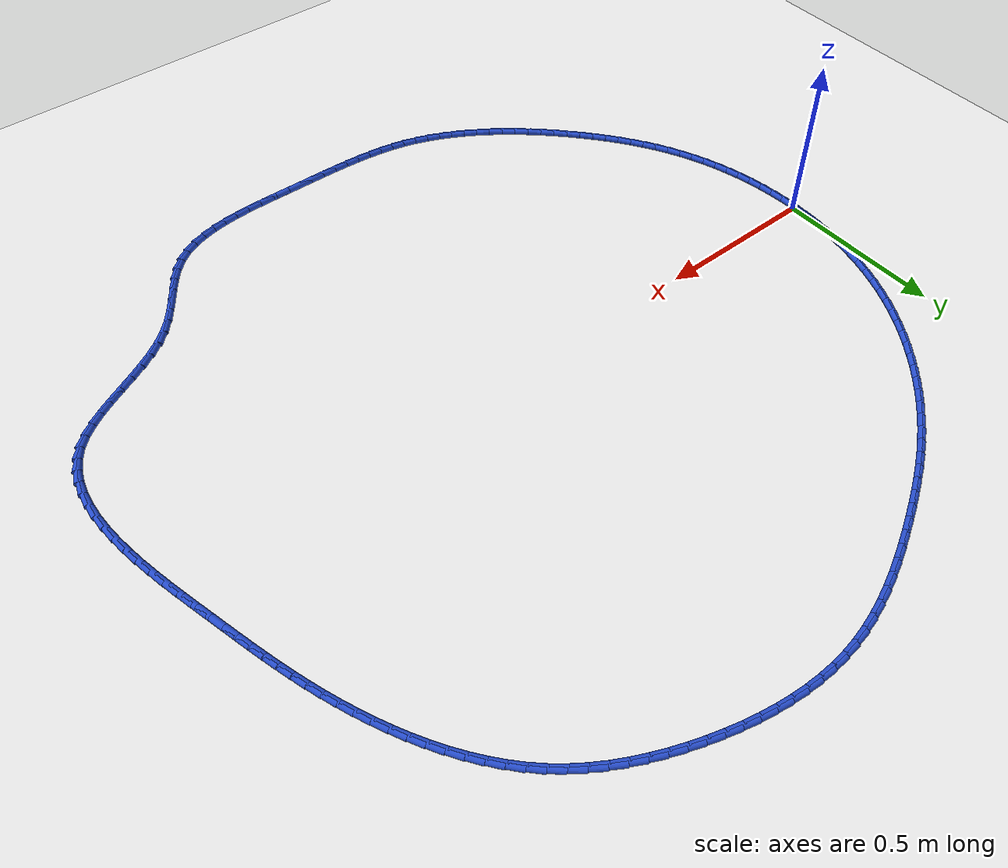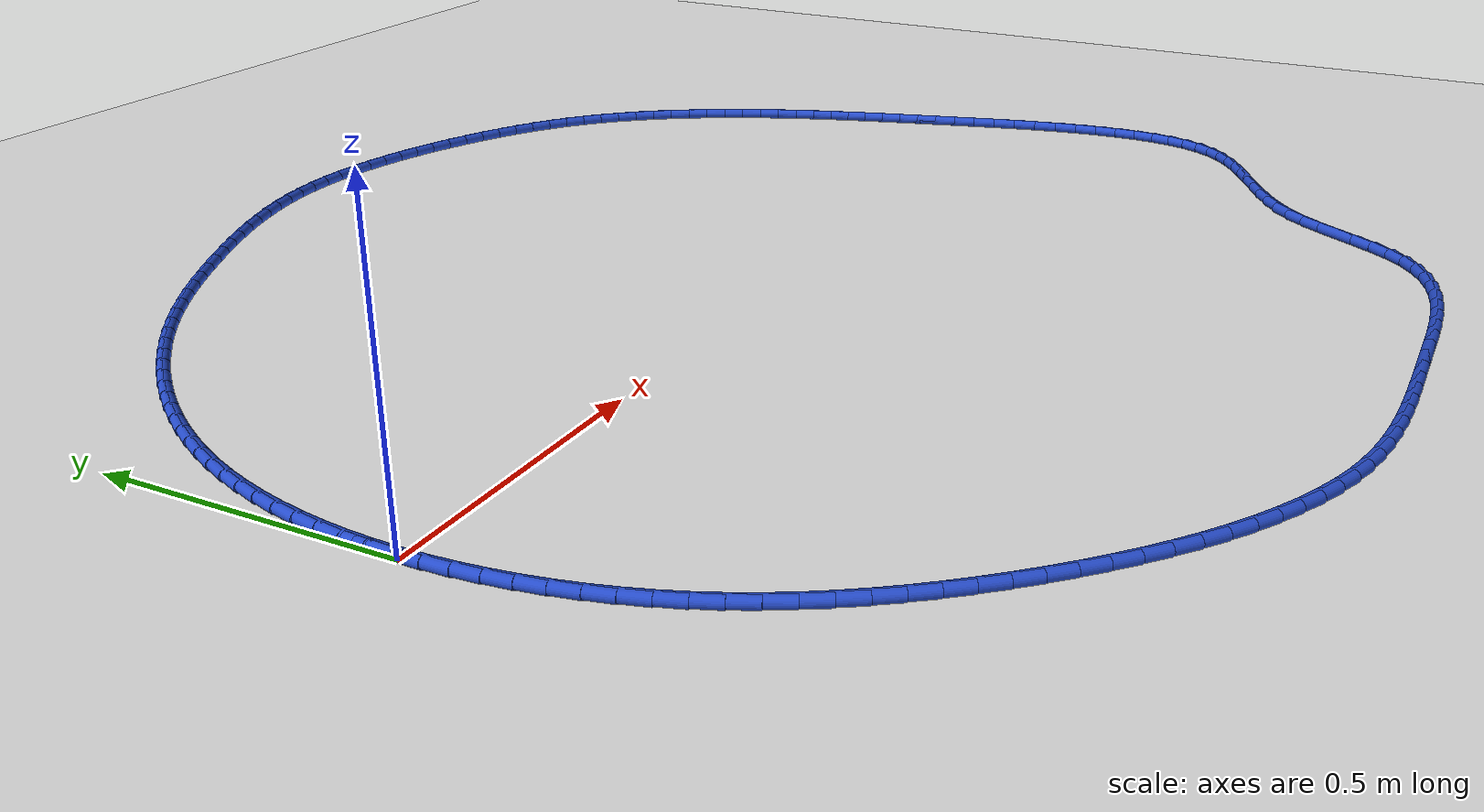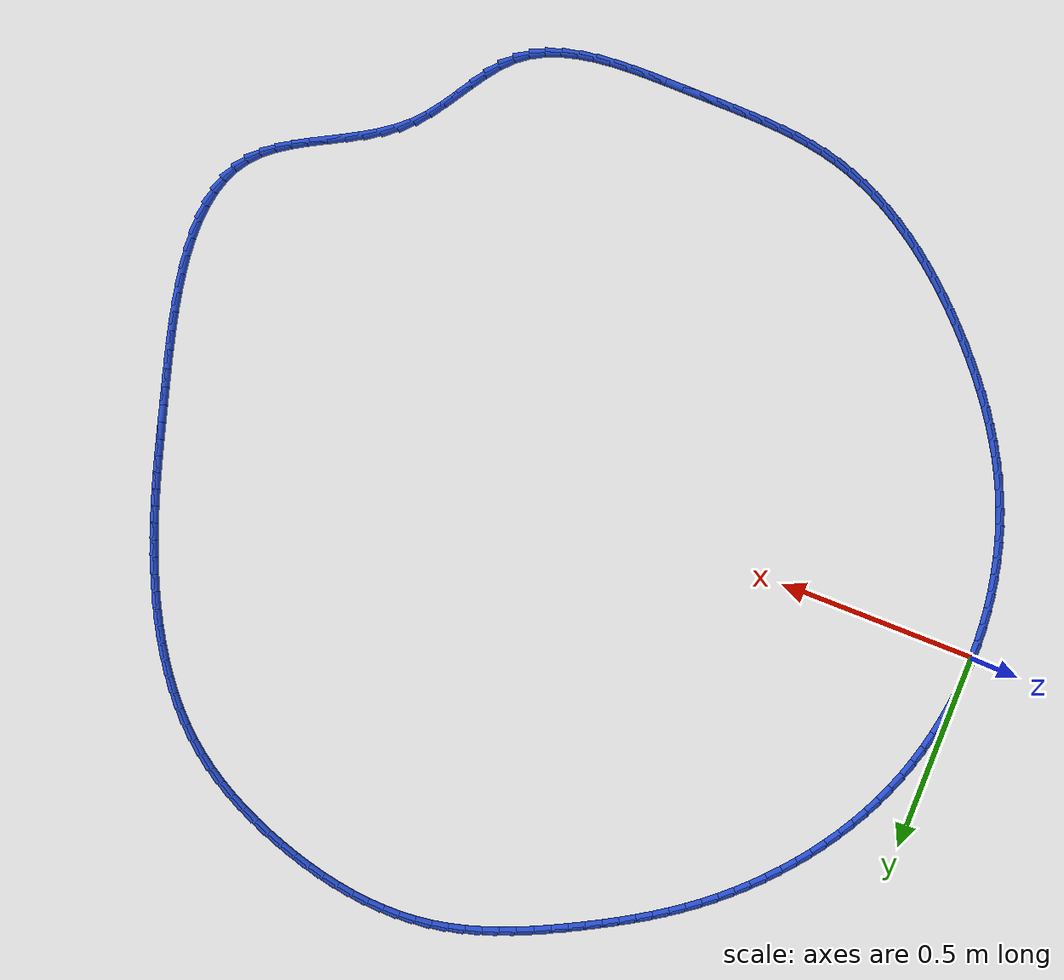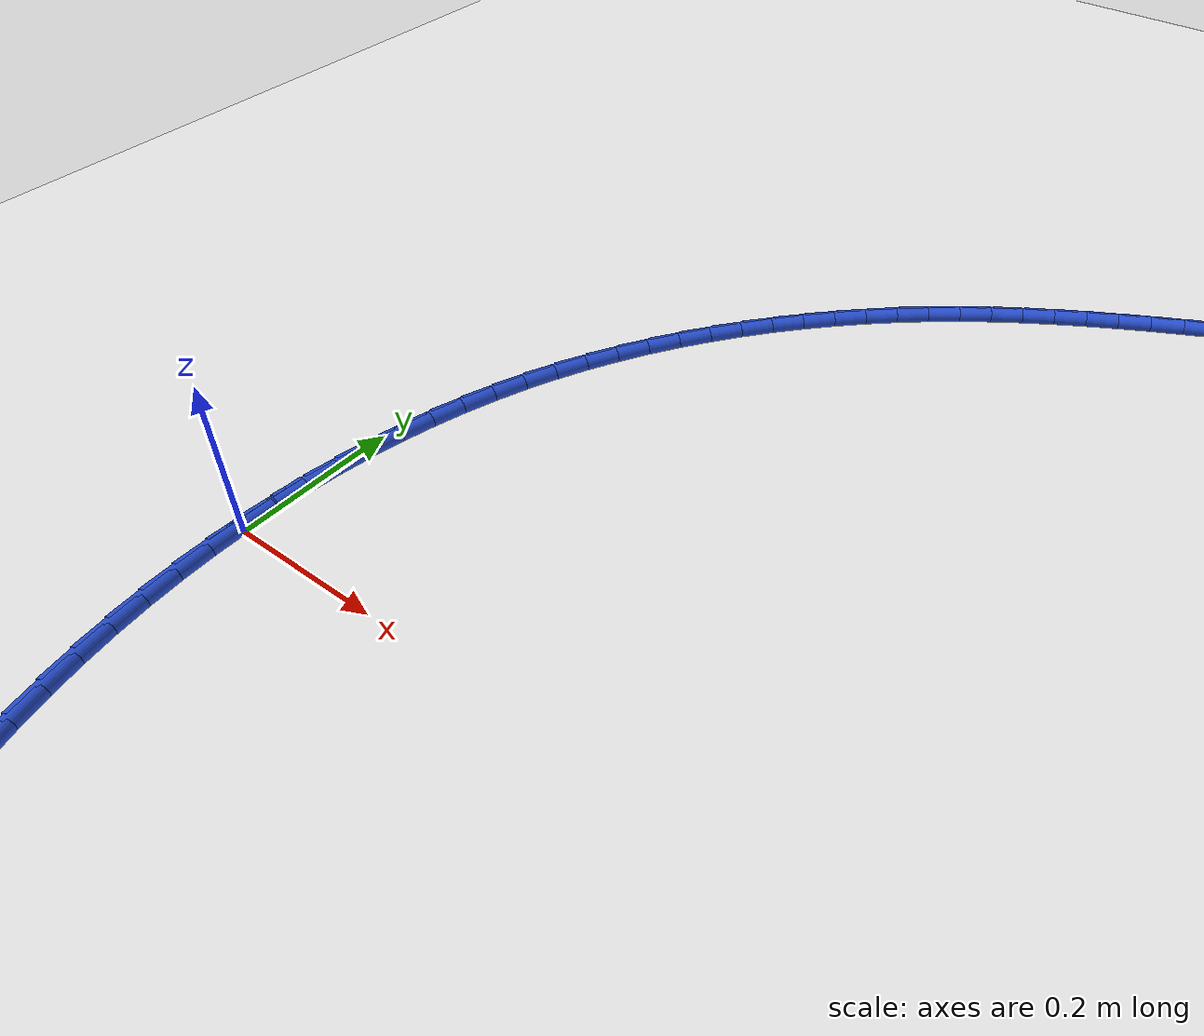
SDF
<sdf version="1.6">
 <world name="default">
  <light name="sun" type="directional">
   <pose>0 0 10 0 -0 0</pose>
   <diffuse>0.8 0.8 0.8 1</diffuse>
   <specular>0.2 0.2 0.2 1</specular>
   <attenuation>
    <range>1000</range>
    <constant>0.9</constant>
    <linear>0.01</linear>
    <quadratic>0.001</quadratic>
   </attenuation>
   <direction>-0.5 0.1 -0.9</direction>
  </light>
  <model name="ground_plane">
   <static>1</static>
   <link name="link">
    <collision name="collision">
     <geometry><plane><normal>0 0 1</normal><size>100 100</size></plane></geometry>
     <surface><friction><ode><mu>100</mu><mu2>50</mu2></ode></friction></surface>
    </collision>
    <visual name="visual">
     <cast_shadows>0</cast_shadows>
     <geometry><plane><normal>0 0 1</normal><size>100 100</size></plane></geometry>
     <material>
      <script><uri>file://media/materials/scripts/gazebo.material</uri><name>Gazebo/WhiteGlow</name></script>
     </material>
    </visual>
   </link>
  </model>
  <gravity>0 0 -9.8</gravity>
  <magnetic_field>6e-06 2.3e-05 -4.2e-05</magnetic_field>
  <atmosphere type="adiabatic"/>
  <physics name="default_physics" default="0" type="ode">
   <max_step_size>0.001</max_step_size>
   <real_time_factor>1</real_time_factor>
   <real_time_update_rate>1000</real_time_update_rate>
  </physics>
  <scene><ambient>0.4 0.4 0.4 1</ambient><background>0.7 0.7 0.7 1</background><shadows>1</shadows></scene>
  <spherical_coordinates>
   <surface_model>EARTH_WGS84</surface_model>
   <latitude_deg>0</latitude_deg>
   <longitude_deg>0</longitude_deg>
   <elevation>0</elevation>
   <heading_deg>0</heading_deg>
  </spherical_coordinates>
  <model name="line">
   <link name="link_0">
    <pose>3.2959746043559335e-17 -6.938893903907228e-17 0.01 0 1.57 1.5512849060006757</pose>
    <collision name="collision">
     <geometry><cylinder><radius>0.01</radius><length>0.08</length></cylinder></geometry>
    </collision>
    <visual name="visual">
     <material>
      <script><name>Gazebo/Blue</name><uri>file://media/materials/scripts/gazebo.material</uri></script>
     </material>
     <geometry><cylinder><radius>0.01</radius><length>0.08</length></cylinder></geometry>
    </visual>
   </link>
   <link name="link_1">
    <pose>0.0008242828212076035 0.04224080998406334 0.01 0 1.57 1.509834602419437</pose>
    <collision name="collision">
     <geometry><cylinder><radius>0.01</radius><length>0.08</length></cylinder></geometry>
    </collision>
    <visual name="visual">
     <material>
      <script><name>Gazebo/Blue</name><uri>file://media/materials/scripts/gazebo.material</uri></script>
     </material>
     <geometry><cylinder><radius>0.01</radius><length>0.08</length></cylinder></geometry>
    </visual>
   </link>
   <link name="link_2">
    <pose>0.0033957350570593997 0.08436996587760281 0.01 0 1.57 1.468045484106311</pose>
    <collision name="collision">
     <geometry><cylinder><radius>0.01</radius><length>0.08</length></cylinder></geometry>
    </collision>
    <visual name="visual">
     <material>
      <script><name>Gazebo/Blue</name><uri>file://media/materials/scripts/gazebo.material</uri></script>
     </material>
     <geometry><cylinder><radius>0.01</radius><length>0.08</length></cylinder></geometry>
    </visual>
   </link>
   <link name="link_3">
    <pose>0.007720835602177713 0.1263148163408653 0.01 0 1.57 1.4258489322903987</pose>
    <collision name="collision">
     <geometry><cylinder><radius>0.01</radius><length>0.08</length></cylinder></geometry>
    </collision>
    <visual name="visual">
     <material>
      <script><name>Gazebo/Blue</name><uri>file://media/materials/scripts/gazebo.material</uri></script>
     </material>
     <geometry><cylinder><radius>0.01</radius><length>0.08</length></cylinder></geometry>
    </visual>
   </link>
   <link name="link_4">
    <pose>0.013806063351184826 0.1680027100340975 0.01 0 1.57 1.3831800137416523</pose>
    <collision name="collision">
     <geometry><cylinder><radius>0.01</radius><length>0.08</length></cylinder></geometry>
    </collision>
    <visual name="visual">
     <material>
      <script><name>Gazebo/Blue</name><uri>file://media/materials/scripts/gazebo.material</uri></script>
     </material>
     <geometry><cylinder><radius>0.01</radius><length>0.08</length></cylinder></geometry>
    </visual>
   </link>
   <link name="link_5">
    <pose>0.02165789719870302 0.20936099561754626 0.01 0 1.57 1.3399785192944504</pose>
    <collision name="collision">
     <geometry><cylinder><radius>0.01</radius><length>0.08</length></cylinder></geometry>
    </collision>
    <visual name="visual">
     <material>
      <script><name>Gazebo/Blue</name><uri>file://media/materials/scripts/gazebo.material</uri></script>
     </material>
     <geometry><cylinder><radius>0.01</radius><length>0.08</length></cylinder></geometry>
    </visual>
   </link>
   <link name="link_6">
    <pose>0.031282816039354594 0.2503170217514585 0.01 0 1.57 1.296190110756127</pose>
    <collision name="collision">
     <geometry><cylinder><radius>0.01</radius><length>0.08</length></cylinder></geometry>
    </collision>
    <visual name="visual">
     <material>
      <script><name>Gazebo/Blue</name><uri>file://media/materials/scripts/gazebo.material</uri></script>
     </material>
     <geometry><cylinder><radius>0.01</radius><length>0.08</length></cylinder></geometry>
    </visual>
   </link>
   <link name="link_7">
    <pose>0.04268729876776183 0.2907981370960808 0.01 0 1.57 1.2517675752675816</pose>
    <collision name="collision">
     <geometry><cylinder><radius>0.01</radius><length>0.08</length></cylinder></geometry>
    </collision>
    <visual name="visual">
     <material>
      <script><name>Gazebo/Blue</name><uri>file://media/materials/scripts/gazebo.material</uri></script>
     </material>
     <geometry><cylinder><radius>0.01</radius><length>0.08</length></cylinder></geometry>
    </visual>
   </link>
   <link name="link_8">
    <pose>0.055877824278547 0.3307316903116603 0.01 0 1.57 1.2066721761818502</pose>
    <collision name="collision">
     <geometry><cylinder><radius>0.01</radius><length>0.08</length></cylinder></geometry>
    </collision>
    <visual name="visual">
     <material>
      <script><name>Gazebo/Blue</name><uri>file://media/materials/scripts/gazebo.material</uri></script>
     </material>
     <geometry><cylinder><radius>0.01</radius><length>0.08</length></cylinder></geometry>
    </visual>
   </link>
   <link name="link_9">
    <pose>0.07086087146633238 0.3700450300584434 0.01 0 1.57 1.1609838515399316</pose>
    <collision name="collision">
     <geometry><cylinder><radius>0.01</radius><length>0.08</length></cylinder></geometry>
    </collision>
    <visual name="visual">
     <material>
      <script><name>Gazebo/Blue</name><uri>file://media/materials/scripts/gazebo.material</uri></script>
     </material>
     <geometry><cylinder><radius>0.01</radius><length>0.08</length></cylinder></geometry>
    </visual>
   </link>
   <link name="link_10">
    <pose>0.0876385577204264 0.4086669607770966 0.01 0 1.57 1.1159029134052514</pose>
    <collision name="collision">
     <geometry><cylinder><radius>0.01</radius><length>0.08</length></cylinder></geometry>
    </collision>
    <visual name="visual">
     <material>
      <script><name>Gazebo/Blue</name><uri>file://media/materials/scripts/gazebo.material</uri></script>
     </material>
     <geometry><cylinder><radius>0.01</radius><length>0.08</length></cylinder></geometry>
    </visual>
   </link>
   <link name="link_11">
    <pose>0.10616376814459691 0.4465427196286702 0.01 0 1.57 1.0721512233106378</pose>
    <collision name="collision">
     <geometry><cylinder><radius>0.01</radius><length>0.08</length></cylinder></geometry>
    </collision>
    <visual name="visual">
     <material>
      <script><name>Gazebo/Blue</name><uri>file://media/materials/scripts/gazebo.material</uri></script>
     </material>
     <geometry><cylinder><radius>0.01</radius><length>0.08</length></cylinder></geometry>
    </visual>
   </link>
   <link name="link_12">
    <pose>0.12635830953603905 0.48362791707125663 0.01 0 1.57 1.0296683034240788</pose>
    <collision name="collision">
     <geometry><cylinder><radius>0.01</radius><length>0.08</length></cylinder></geometry>
    </collision>
    <visual name="visual">
     <material>
      <script><name>Gazebo/Blue</name><uri>file://media/materials/scripts/gazebo.material</uri></script>
     </material>
     <geometry><cylinder><radius>0.01</radius><length>0.08</length></cylinder></geometry>
    </visual>
   </link>
   <link name="link_13">
    <pose>0.14814350062086085 0.5198783264709993 0.01 0 1.57 0.9883684102926094</pose>
    <collision name="collision">
     <geometry><cylinder><radius>0.01</radius><length>0.08</length></cylinder></geometry>
    </collision>
    <visual name="visual">
     <material>
      <script><name>Gazebo/Blue</name><uri>file://media/materials/scripts/gazebo.material</uri></script>
     </material>
     <geometry><cylinder><radius>0.01</radius><length>0.08</length></cylinder></geometry>
    </visual>
   </link>
   <link name="link_14">
    <pose>0.17144066012517065 0.5552497211940419 0.01 0 1.57 0.9481554389620419</pose>
    <collision name="collision">
     <geometry><cylinder><radius>0.01</radius><length>0.08</length></cylinder></geometry>
    </collision>
    <visual name="visual">
     <material>
      <script><name>Gazebo/Blue</name><uri>file://media/materials/scripts/gazebo.material</uri></script>
     </material>
     <geometry><cylinder><radius>0.01</radius><length>0.08</length></cylinder></geometry>
    </visual>
   </link>
   <link name="link_15">
    <pose>0.19617110677507654 0.589697874606528 0.01 0 1.57 0.9089251842007465</pose>
    <collision name="collision">
     <geometry><cylinder><radius>0.01</radius><length>0.08</length></cylinder></geometry>
    </collision>
    <visual name="visual">
     <material>
      <script><name>Gazebo/Blue</name><uri>file://media/materials/scripts/gazebo.material</uri></script>
     </material>
     <geometry><cylinder><radius>0.01</radius><length>0.08</length></cylinder></geometry>
    </visual>
   </link>
   <link name="link_16">
    <pose>0.22225615929668677 0.6231785600746013 0.01 0 1.57 0.8705671381486784</pose>
    <collision name="collision">
     <geometry><cylinder><radius>0.01</radius><length>0.08</length></cylinder></geometry>
    </collision>
    <visual name="visual">
     <material>
      <script><name>Gazebo/Blue</name><uri>file://media/materials/scripts/gazebo.material</uri></script>
     </material>
     <geometry><cylinder><radius>0.01</radius><length>0.08</length></cylinder></geometry>
    </visual>
   </link>
   <link name="link_17">
    <pose>0.2496171364161094 0.655647550964405 0.01 0 1.57 0.8329658527944049</pose>
    <collision name="collision">
     <geometry><cylinder><radius>0.01</radius><length>0.08</length></cylinder></geometry>
    </collision>
    <visual name="visual">
     <material>
      <script><name>Gazebo/Blue</name><uri>file://media/materials/scripts/gazebo.material</uri></script>
     </material>
     <geometry><cylinder><radius>0.01</radius><length>0.08</length></cylinder></geometry>
    </visual>
   </link>
   <link name="link_18">
    <pose>0.2781753568594526 0.6870606206420827 0.01 0 1.57 0.7960019078720568</pose>
    <collision name="collision">
     <geometry><cylinder><radius>0.01</radius><length>0.08</length></cylinder></geometry>
    </collision>
    <visual name="visual">
     <material>
      <script><name>Gazebo/Blue</name><uri>file://media/materials/scripts/gazebo.material</uri></script>
     </material>
     <geometry><cylinder><radius>0.01</radius><length>0.08</length></cylinder></geometry>
    </visual>
   </link>
   <link name="link_19">
    <pose>0.3078521393528247 0.7173735424737784 0.01 0 1.57 0.7595525301584132</pose>
    <collision name="collision">
     <geometry><cylinder><radius>0.01</radius><length>0.08</length></cylinder></geometry>
    </collision>
    <visual name="visual">
     <material>
      <script><name>Gazebo/Blue</name><uri>file://media/materials/scripts/gazebo.material</uri></script>
     </material>
     <geometry><cylinder><radius>0.01</radius><length>0.08</length></cylinder></geometry>
    </visual>
   </link>
   <link name="link_20">
    <pose>0.3385688026223335 0.7465420898256352 0.01 0 1.57 0.7234919110220336</pose>
    <collision name="collision">
     <geometry><cylinder><radius>0.01</radius><length>0.08</length></cylinder></geometry>
    </collision>
    <visual name="visual">
     <material>
      <script><name>Gazebo/Blue</name><uri>file://media/materials/scripts/gazebo.material</uri></script>
     </material>
     <geometry><cylinder><radius>0.01</radius><length>0.08</length></cylinder></geometry>
    </visual>
   </link>
   <link name="link_21">
    <pose>0.3702466653940877 0.7745220360637969 0.01 0 1.57 0.6876912673341857</pose>
    <collision name="collision">
     <geometry><cylinder><radius>0.01</radius><length>0.08</length></cylinder></geometry>
    </collision>
    <visual name="visual">
     <material>
      <script><name>Gazebo/Blue</name><uri>file://media/materials/scripts/gazebo.material</uri></script>
     </material>
     <geometry><cylinder><radius>0.01</radius><length>0.08</length></cylinder></geometry>
    </visual>
   </link>
   <link name="link_22">
    <pose>0.4028070463941952 0.8012691545544071 0.01 0 1.57 0.652047848712966</pose>
    <collision name="collision">
     <geometry><cylinder><radius>0.01</radius><length>0.08</length></cylinder></geometry>
    </collision>
    <visual name="visual">
     <material>
      <script><name>Gazebo/Blue</name><uri>file://media/materials/scripts/gazebo.material</uri></script>
     </material>
     <geometry><cylinder><radius>0.01</radius><length>0.08</length></cylinder></geometry>
    </visual>
   </link>
   <link name="link_23">
    <pose>0.4361715927601685 0.8267410093369945 0.01 0 1.57 0.6176382299849696</pose>
    <collision name="collision">
     <geometry><cylinder><radius>0.01</radius><length>0.08</length></cylinder></geometry>
    </collision>
    <visual name="visual">
     <material>
      <script><name>Gazebo/Blue</name><uri>file://media/materials/scripts/gazebo.material</uri></script>
     </material>
     <geometry><cylinder><radius>0.01</radius><length>0.08</length></cylinder></geometry>
    </visual>
   </link>
   <link name="link_24">
    <pose>0.4702750078280039 0.8509663537789308 0.01 0 1.57 0.5861081815767222</pose>
    <collision name="collision">
     <geometry><cylinder><radius>0.01</radius><length>0.08</length></cylinder></geometry>
    </collision>
    <visual name="visual">
     <material>
      <script><name>Gazebo/Blue</name><uri>file://media/materials/scripts/gazebo.material</uri></script>
     </material>
     <geometry><cylinder><radius>0.01</radius><length>0.08</length></cylinder></geometry>
    </visual>
   </link>
   <link name="link_25">
    <pose>0.5050691246298507 0.874067341448023 0.01 0 1.57 0.5577158613599267</pose>
    <collision name="collision">
     <geometry><cylinder><radius>0.01</radius><length>0.08</length></cylinder></geometry>
    </collision>
    <visual name="visual">
     <material>
      <script><name>Gazebo/Blue</name><uri>file://media/materials/scripts/gazebo.material</uri></script>
     </material>
     <geometry><cylinder><radius>0.01</radius><length>0.08</length></cylinder></geometry>
    </visual>
   </link>
   <link name="link_26">
    <pose>0.540506938187632 0.8961724616974174 0.01 0 1.57 0.5325684235892796</pose>
    <collision name="collision">
     <geometry><cylinder><radius>0.01</radius><length>0.08</length></cylinder></geometry>
    </collision>
    <visual name="visual">
     <material>
      <script><name>Gazebo/Blue</name><uri>file://media/materials/scripts/gazebo.material</uri></script>
     </material>
     <geometry><cylinder><radius>0.01</radius><length>0.08</length></cylinder></geometry>
    </visual>
   </link>
   <link name="link_27">
    <pose>0.5765414435232702 0.9174102038802594 0.01 0 1.57 0.5107318718283449</pose>
    <collision name="collision">
     <geometry><cylinder><radius>0.01</radius><length>0.08</length></cylinder></geometry>
    </collision>
    <visual name="visual">
     <material>
      <script><name>Gazebo/Blue</name><uri>file://media/materials/scripts/gazebo.material</uri></script>
     </material>
     <geometry><cylinder><radius>0.01</radius><length>0.08</length></cylinder></geometry>
    </visual>
   </link>
   <link name="link_28">
    <pose>0.6131256356586886 0.9379090573496964 0.01 0 1.57 0.4922382776769991</pose>
    <collision name="collision">
     <geometry><cylinder><radius>0.01</radius><length>0.08</length></cylinder></geometry>
    </collision>
    <visual name="visual">
     <material>
      <script><name>Gazebo/Blue</name><uri>file://media/materials/scripts/gazebo.material</uri></script>
     </material>
     <geometry><cylinder><radius>0.01</radius><length>0.08</length></cylinder></geometry>
    </visual>
   </link>
   <link name="link_29">
    <pose>0.6502125096158097 0.9577975114588738 0.01 0 1.57 0.47680738269793166</pose>
    <collision name="collision">
     <geometry><cylinder><radius>0.01</radius><length>0.08</length></cylinder></geometry>
    </collision>
    <visual name="visual">
     <material>
      <script><name>Gazebo/Blue</name><uri>file://media/materials/scripts/gazebo.material</uri></script>
     </material>
     <geometry><cylinder><radius>0.01</radius><length>0.08</length></cylinder></geometry>
    </visual>
   </link>
   <link name="link_30">
    <pose>0.6877564398547987 0.9771911903062086 0.01 0 1.57 0.459928320298955</pose>
    <collision name="collision">
     <geometry><cylinder><radius>0.01</radius><length>0.08</length></cylinder></geometry>
    </collision>
    <visual name="visual">
     <material>
      <script><name>Gazebo/Blue</name><uri>file://media/materials/scripts/gazebo.material</uri></script>
     </material>
     <geometry><cylinder><radius>0.01</radius><length>0.08</length></cylinder></geometry>
    </visual>
   </link>
   <link name="link_31">
    <pose>0.7257334851553422 0.9960034803793862 0.01 0 1.57 0.43794896306137965</pose>
    <collision name="collision">
     <geometry><cylinder><radius>0.01</radius><length>0.08</length></cylinder></geometry>
    </collision>
    <visual name="visual">
     <material>
      <script><name>Gazebo/Blue</name><uri>file://media/materials/scripts/gazebo.material</uri></script>
     </material>
     <geometry><cylinder><radius>0.01</radius><length>0.08</length></cylinder></geometry>
    </visual>
   </link>
   <link name="link_32">
    <pose>0.7641369474424401 1.0139869509217943 0.01 0 1.57 0.4106238354148397</pose>
    <collision name="collision">
     <geometry><cylinder><radius>0.01</radius><length>0.08</length></cylinder></geometry>
    </collision>
    <visual name="visual">
     <material>
      <script><name>Gazebo/Blue</name><uri>file://media/materials/scripts/gazebo.material</uri></script>
     </material>
     <geometry><cylinder><radius>0.01</radius><length>0.08</length></cylinder></geometry>
    </visual>
   </link>
   <link name="link_33">
    <pose>0.8029606051948389 1.0308897266245778 0.01 0 1.57 0.37776042198000903</pose>
    <collision name="collision">
     <geometry><cylinder><radius>0.01</radius><length>0.08</length></cylinder></geometry>
    </collision>
    <visual name="visual">
     <material>
      <script><name>Gazebo/Blue</name><uri>file://media/materials/scripts/gazebo.material</uri></script>
     </material>
     <geometry><cylinder><radius>0.01</radius><length>0.08</length></cylinder></geometry>
    </visual>
   </link>
   <link name="link_34">
    <pose>0.8421982368912844 1.0464599321788823 0.01 0 1.57 0.33914169063123706</pose>
    <collision name="collision">
     <geometry><cylinder><radius>0.01</radius><length>0.08</length></cylinder></geometry>
    </collision>
    <visual name="visual">
     <material>
      <script><name>Gazebo/Blue</name><uri>file://media/materials/scripts/gazebo.material</uri></script>
     </material>
     <geometry><cylinder><radius>0.01</radius><length>0.08</length></cylinder></geometry>
    </visual>
   </link>
   <link name="link_35">
    <pose>0.8818436210105229 1.0604456922758538 0.01 0 1.57 0.29455496292605493</pose>
    <collision name="collision">
     <geometry><cylinder><radius>0.01</radius><length>0.08</length></cylinder></geometry>
    </collision>
    <visual name="visual">
     <material>
      <script><name>Gazebo/Blue</name><uri>file://media/materials/scripts/gazebo.material</uri></script>
     </material>
     <geometry><cylinder><radius>0.01</radius><length>0.08</length></cylinder></geometry>
    </visual>
   </link>
   <link name="link_36">
    <pose>0.9218905360313012 1.072595131606638 0.01 0 1.57 0.2438307196376346</pose>
    <collision name="collision">
     <geometry><cylinder><radius>0.01</radius><length>0.08</length></cylinder></geometry>
    </collision>
    <visual name="visual">
     <material>
      <script><name>Gazebo/Blue</name><uri>file://media/materials/scripts/gazebo.material</uri></script>
     </material>
     <geometry><cylinder><radius>0.01</radius><length>0.08</length></cylinder></geometry>
    </visual>
   </link>
   <link name="link_37">
    <pose>0.9623327604323648 1.0826563748623794 0.01 0 1.57 0.1868924690653987</pose>
    <collision name="collision">
     <geometry><cylinder><radius>0.01</radius><length>0.08</length></cylinder></geometry>
    </collision>
    <visual name="visual">
     <material>
      <script><name>Gazebo/Blue</name><uri>file://media/materials/scripts/gazebo.material</uri></script>
     </material>
     <geometry><cylinder><radius>0.01</radius><length>0.08</length></cylinder></geometry>
    </visual>
   </link>
   <link name="link_38">
    <pose>1.00316407269246 1.0903775467342243 0.01 0 1.57 0.12420744232587441</pose>
    <collision name="collision">
     <geometry><cylinder><radius>0.01</radius><length>0.08</length></cylinder></geometry>
    </collision>
    <visual name="visual">
     <material>
      <script><name>Gazebo/Blue</name><uri>file://media/materials/scripts/gazebo.material</uri></script>
     </material>
     <geometry><cylinder><radius>0.01</radius><length>0.08</length></cylinder></geometry>
    </visual>
   </link>
   <link name="link_39">
    <pose>1.0443745443226686 1.095522680094361 0.01 0 1.57 0.061279632909692</pose>
    <collision name="collision">
     <geometry><cylinder><radius>0.01</radius><length>0.08</length></cylinder></geometry>
    </collision>
    <visual name="visual">
     <material>
      <script><name>Gazebo/Blue</name><uri>file://media/materials/scripts/gazebo.material</uri></script>
     </material>
     <geometry><cylinder><radius>0.01</radius><length>0.08</length></cylinder></geometry>
    </visual>
   </link>
   <link name="link_40">
    <pose>1.0859041512149763 1.0980707895062725 0.01 0 1.57 0.0020248489382844845</pose>
    <collision name="collision">
     <geometry><cylinder><radius>0.01</radius><length>0.08</length></cylinder></geometry>
    </collision>
    <visual name="visual">
     <material>
      <script><name>Gazebo/Blue</name><uri>file://media/materials/scripts/gazebo.material</uri></script>
     </material>
     <geometry><cylinder><radius>0.01</radius><length>0.08</length></cylinder></geometry>
    </visual>
   </link>
   <link name="link_41">
    <pose>1.1276568805194542 1.0981553325914177 0.01 0 1.57 -0.053488393881848506</pose>
    <collision name="collision">
     <geometry><cylinder><radius>0.01</radius><length>0.08</length></cylinder></geometry>
    </collision>
    <visual name="visual">
     <material>
      <script><name>Gazebo/Blue</name><uri>file://media/materials/scripts/gazebo.material</uri></script>
     </material>
     <geometry><cylinder><radius>0.01</radius><length>0.08</length></cylinder></geometry>
    </visual>
   </link>
   <link name="link_42">
    <pose>1.1695359308908102 1.09591315074152 0.01 0 1.57 -0.1053639454663621</pose>
    <collision name="collision">
     <geometry><cylinder><radius>0.01</radius><length>0.08</length></cylinder></geometry>
    </collision>
    <visual name="visual">
     <material>
      <script><name>Gazebo/Blue</name><uri>file://media/materials/scripts/gazebo.material</uri></script>
     </material>
     <geometry><cylinder><radius>0.01</radius><length>0.08</length></cylinder></geometry>
    </visual>
   </link>
   <link name="link_43">
    <pose>1.2114445009837551 1.0914810853483048 0.01 0 1.57 -0.15376948117144418</pose>
    <collision name="collision">
     <geometry><cylinder><radius>0.01</radius><length>0.08</length></cylinder></geometry>
    </collision>
    <visual name="visual">
     <material>
      <script><name>Gazebo/Blue</name><uri>file://media/materials/scripts/gazebo.material</uri></script>
     </material>
     <geometry><cylinder><radius>0.01</radius><length>0.08</length></cylinder></geometry>
    </visual>
   </link>
   <link name="link_44">
    <pose>1.2532857894529976 1.084995977803495 0.01 0 1.57 -0.19891472501962215</pose>
    <collision name="collision">
     <geometry><cylinder><radius>0.01</radius><length>0.08</length></cylinder></geometry>
    </collision>
    <visual name="visual">
     <material>
      <script><name>Gazebo/Blue</name><uri>file://media/materials/scripts/gazebo.material</uri></script>
     </material>
     <geometry><cylinder><radius>0.01</radius><length>0.08</length></cylinder></geometry>
    </visual>
   </link>
   <link name="link_45">
    <pose>1.2949629949532466 1.0765946694988149 0.01 0 1.57 -0.24103403496015072</pose>
    <collision name="collision">
     <geometry><cylinder><radius>0.01</radius><length>0.08</length></cylinder></geometry>
    </collision>
    <visual name="visual">
     <material>
      <script><name>Gazebo/Blue</name><uri>file://media/materials/scripts/gazebo.material</uri></script>
     </material>
     <geometry><cylinder><radius>0.01</radius><length>0.08</length></cylinder></geometry>
    </visual>
   </link>
   <link name="link_46">
    <pose>1.336379316139213 1.0664140018259893 0.01 0 1.57 -0.28037332376972135</pose>
    <collision name="collision">
     <geometry><cylinder><radius>0.01</radius><length>0.08</length></cylinder></geometry>
    </collision>
    <visual name="visual">
     <material>
      <script><name>Gazebo/Blue</name><uri>file://media/materials/scripts/gazebo.material</uri></script>
     </material>
     <geometry><cylinder><radius>0.01</radius><length>0.08</length></cylinder></geometry>
    </visual>
   </link>
   <link name="link_47">
    <pose>1.377437951665604 1.0545908161767419 0.01 0 1.57 -0.3171808374756045</pose>
    <collision name="collision">
     <geometry><cylinder><radius>0.01</radius><length>0.08</length></cylinder></geometry>
    </collision>
    <visual name="visual">
     <material>
      <script><name>Gazebo/Blue</name><uri>file://media/materials/scripts/gazebo.material</uri></script>
     </material>
     <geometry><cylinder><radius>0.01</radius><length>0.08</length></cylinder></geometry>
    </visual>
   </link>
   <link name="link_48">
    <pose>1.4180421001871304 1.0412619539427965 0.01 0 1.57 -0.35192389397606794</pose>
    <collision name="collision">
     <geometry><cylinder><radius>0.01</radius><length>0.08</length></cylinder></geometry>
    </collision>
    <visual name="visual">
     <material>
      <script><name>Gazebo/Blue</name><uri>file://media/materials/scripts/gazebo.material</uri></script>
     </material>
     <geometry><cylinder><radius>0.01</radius><length>0.08</length></cylinder></geometry>
    </visual>
   </link>
   <link name="link_49">
    <pose>1.4580929541964442 1.0265548688478368 0.01 0 1.57 -0.3878942419663834</pose>
    <collision name="collision">
     <geometry><cylinder><radius>0.01</radius><length>0.08</length></cylinder></geometry>
    </collision>
    <visual name="visual">
     <material>
      <script><name>Gazebo/Blue</name><uri>file://media/materials/scripts/gazebo.material</uri></script>
     </material>
     <geometry><cylinder><radius>0.01</radius><length>0.08</length></cylinder></geometry>
    </visual>
   </link>
   <link name="link_50">
    <pose>1.4974641320047304 1.0104679835329133 0.01 0 1.57 -0.42752070435544054</pose>
    <collision name="collision">
     <geometry><cylinder><radius>0.01</radius><length>0.08</length></cylinder></geometry>
    </collision>
    <visual name="visual">
     <material>
      <script><name>Gazebo/Blue</name><uri>file://media/materials/scripts/gazebo.material</uri></script>
     </material>
     <geometry><cylinder><radius>0.01</radius><length>0.08</length></cylinder></geometry>
    </visual>
   </link>
   <link name="link_51">
    <pose>1.5360092096523785 0.9929059345043197 0.01 0 1.57 -0.4710433658986751</pose>
    <collision name="collision">
     <geometry><cylinder><radius>0.01</radius><length>0.08</length></cylinder></geometry>
    </collision>
    <visual name="visual">
     <material>
      <script><name>Gazebo/Blue</name><uri>file://media/materials/scripts/gazebo.material</uri></script>
     </material>
     <geometry><cylinder><radius>0.01</radius><length>0.08</length></cylinder></geometry>
    </visual>
   </link>
   <link name="link_52">
    <pose>1.5735813116286221 0.9737712452723644 0.01 0 1.57 -0.5186278829530047</pose>
    <collision name="collision">
     <geometry><cylinder><radius>0.01</radius><length>0.08</length></cylinder></geometry>
    </collision>
    <visual name="visual">
     <material>
      <script><name>Gazebo/Blue</name><uri>file://media/materials/scripts/gazebo.material</uri></script>
     </material>
     <geometry><cylinder><radius>0.01</radius><length>0.08</length></cylinder></geometry>
    </visual>
   </link>
   <link name="link_53">
    <pose>1.610033562422693 0.9529664393473535 0.01 0 1.57 -0.5703944252641756</pose>
    <collision name="collision">
     <geometry><cylinder><radius>0.01</radius><length>0.08</length></cylinder></geometry>
    </collision>
    <visual name="visual">
     <material>
      <script><name>Gazebo/Blue</name><uri>file://media/materials/scripts/gazebo.material</uri></script>
     </material>
     <geometry><cylinder><radius>0.01</radius><length>0.08</length></cylinder></geometry>
    </visual>
   </link>
   <link name="link_54">
    <pose>1.645219086523824 0.9303940402395947 0.01 0 1.57 -0.6263919868194499</pose>
    <collision name="collision">
     <geometry><cylinder><radius>0.01</radius><length>0.08</length></cylinder></geometry>
    </collision>
    <visual name="visual">
     <material>
      <script><name>Gazebo/Blue</name><uri>file://media/materials/scripts/gazebo.material</uri></script>
     </material>
     <geometry><cylinder><radius>0.01</radius><length>0.08</length></cylinder></geometry>
    </visual>
   </link>
   <link name="link_55">
    <pose>1.6789910084212474 0.9059565714593957 0.01 0 1.57 -0.6865693831486038</pose>
    <collision name="collision">
     <geometry><cylinder><radius>0.01</radius><length>0.08</length></cylinder></geometry>
    </collision>
    <visual name="visual">
     <material>
      <script><name>Gazebo/Blue</name><uri>file://media/materials/scripts/gazebo.material</uri></script>
     </material>
     <geometry><cylinder><radius>0.01</radius><length>0.08</length></cylinder></geometry>
    </visual>
   </link>
   <link name="link_56">
    <pose>1.711202453608887 0.8795565579104396 0.01 0 1.57 -0.7492569197214123</pose>
    <collision name="collision">
     <geometry><cylinder><radius>0.01</radius><length>0.08</length></cylinder></geometry>
    </collision>
    <visual name="visual">
     <material>
      <script><name>Gazebo/Blue</name><uri>file://media/materials/scripts/gazebo.material</uri></script>
     </material>
     <geometry><cylinder><radius>0.01</radius><length>0.08</length></cylinder></geometry>
    </visual>
   </link>
   <link name="link_57">
    <pose>1.7417431614210928 0.8511473031676515 0.01 0 1.57 -0.8088338215925488</pose>
    <collision name="collision">
     <geometry><cylinder><radius>0.01</radius><length>0.08</length></cylinder></geometry>
    </collision>
    <visual name="visual">
     <material>
      <script><name>Gazebo/Blue</name><uri>file://media/materials/scripts/gazebo.material</uri></script>
     </material>
     <geometry><cylinder><radius>0.01</radius><length>0.08</length></cylinder></geometry>
    </visual>
   </link>
   <link name="link_58">
    <pose>1.7706362943166303 0.8208671514597528 0.01 0 1.57 -0.8640526660216821</pose>
    <collision name="collision">
     <geometry><cylinder><radius>0.01</radius><length>0.08</length></cylinder></geometry>
    </collision>
    <visual name="visual">
     <material>
      <script><name>Gazebo/Blue</name><uri>file://media/materials/scripts/gazebo.material</uri></script>
     </material>
     <geometry><cylinder><radius>0.01</radius><length>0.08</length></cylinder></geometry>
    </visual>
   </link>
   <link name="link_59">
    <pose>1.7979353977059616 0.7888965842482031 0.01 0 1.57 -0.915018374360747</pose>
    <collision name="collision">
     <geometry><cylinder><radius>0.01</radius><length>0.08</length></cylinder></geometry>
    </collision>
    <visual name="visual">
     <material>
      <script><name>Gazebo/Blue</name><uri>file://media/materials/scripts/gazebo.material</uri></script>
     </material>
     <geometry><cylinder><radius>0.01</radius><length>0.08</length></cylinder></geometry>
    </visual>
   </link>
   <link name="link_60">
    <pose>1.8236940169995473 0.7554160829944615 0.01 0 1.57 -0.9619098745434498</pose>
    <collision name="collision">
     <geometry><cylinder><radius>0.01</radius><length>0.08</length></cylinder></geometry>
    </collision>
    <visual name="visual">
     <material>
      <script><name>Gazebo/Blue</name><uri>file://media/materials/scripts/gazebo.material</uri></script>
     </material>
     <geometry><cylinder><radius>0.01</radius><length>0.08</length></cylinder></geometry>
    </visual>
   </link>
   <link name="link_61">
    <pose>1.8479656976078502 0.7206061291599871 0.01 0 1.57 -1.0049516961673555</pose>
    <collision name="collision">
     <geometry><cylinder><radius>0.01</radius><length>0.08</length></cylinder></geometry>
    </collision>
    <visual name="visual">
     <material>
      <script><name>Gazebo/Blue</name><uri>file://media/materials/scripts/gazebo.material</uri></script>
     </material>
     <geometry><cylinder><radius>0.01</radius><length>0.08</length></cylinder></geometry>
    </visual>
   </link>
   <link name="link_62">
    <pose>1.8708039849413316 0.6846472042062395 0.01 0 1.57 -1.0443914623911994</pose>
    <collision name="collision">
     <geometry><cylinder><radius>0.01</radius><length>0.08</length></cylinder></geometry>
    </collision>
    <visual name="visual">
     <material>
      <script><name>Gazebo/Blue</name><uri>file://media/materials/scripts/gazebo.material</uri></script>
     </material>
     <geometry><cylinder><radius>0.01</radius><length>0.08</length></cylinder></geometry>
    </visual>
   </link>
   <link name="link_63">
    <pose>1.8922624244104518 0.6477197895946778 0.01 0 1.57 -1.0804830885034025</pose>
    <collision name="collision">
     <geometry><cylinder><radius>0.01</radius><length>0.08</length></cylinder></geometry>
    </collision>
    <visual name="visual">
     <material>
      <script><name>Gazebo/Blue</name><uri>file://media/materials/scripts/gazebo.material</uri></script>
     </material>
     <geometry><cylinder><radius>0.01</radius><length>0.08</length></cylinder></geometry>
    </visual>
   </link>
   <link name="link_64">
    <pose>1.9123945614256739 0.6100043667867615 0.01 0 1.57 -1.1134748763608069</pose>
    <collision name="collision">
     <geometry><cylinder><radius>0.01</radius><length>0.08</length></cylinder></geometry>
    </collision>
    <visual name="visual">
     <material>
      <script><name>Gazebo/Blue</name><uri>file://media/materials/scripts/gazebo.material</uri></script>
     </material>
     <geometry><cylinder><radius>0.01</radius><length>0.08</length></cylinder></geometry>
    </visual>
   </link>
   <link name="link_65">
    <pose>1.931253941397458 0.5716814172439498 0.01 0 1.57 -1.1436014759672746</pose>
    <collision name="collision">
     <geometry><cylinder><radius>0.01</radius><length>0.08</length></cylinder></geometry>
    </collision>
    <visual name="visual">
     <material>
      <script><name>Gazebo/Blue</name><uri>file://media/materials/scripts/gazebo.material</uri></script>
     </material>
     <geometry><cylinder><radius>0.01</radius><length>0.08</length></cylinder></geometry>
    </visual>
   </link>
   <link name="link_66">
    <pose>1.948894109736267 0.5329314224277014 0.01 0 1.57 -1.1710787005650325</pose>
    <collision name="collision">
     <geometry><cylinder><radius>0.01</radius><length>0.08</length></cylinder></geometry>
    </collision>
    <visual name="visual">
     <material>
      <script><name>Gazebo/Blue</name><uri>file://media/materials/scripts/gazebo.material</uri></script>
     </material>
     <geometry><cylinder><radius>0.01</radius><length>0.08</length></cylinder></geometry>
    </visual>
   </link>
   <link name="link_67">
    <pose>1.9653686118525615 0.4939348637994765 0.01 0 1.57 -1.196100303893416</pose>
    <collision name="collision">
     <geometry><cylinder><radius>0.01</radius><length>0.08</length></cylinder></geometry>
    </collision>
    <visual name="visual">
     <material>
      <script><name>Gazebo/Blue</name><uri>file://media/materials/scripts/gazebo.material</uri></script>
     </material>
     <geometry><cylinder><radius>0.01</radius><length>0.08</length></cylinder></geometry>
    </visual>
   </link>
   <link name="link_68">
    <pose>1.9807309931568036 0.4548722228207336 0.01 0 1.57 -1.2188362346635866</pose>
    <collision name="collision">
     <geometry><cylinder><radius>0.01</radius><length>0.08</length></cylinder></geometry>
    </collision>
    <visual name="visual">
     <material>
      <script><name>Gazebo/Blue</name><uri>file://media/materials/scripts/gazebo.material</uri></script>
     </material>
     <geometry><cylinder><radius>0.01</radius><length>0.08</length></cylinder></geometry>
    </visual>
   </link>
   <link name="link_69">
    <pose>1.995035281477548 0.41592263651237743 0.01 0 1.57 -1.2393833951507676</pose>
    <collision name="collision">
     <geometry><cylinder><radius>0.01</radius><length>0.08</length></cylinder></geometry>
    </collision>
    <visual name="visual">
     <material>
      <script><name>Gazebo/Blue</name><uri>file://media/materials/scripts/gazebo.material</uri></script>
     </material>
     <geometry><cylinder><radius>0.01</radius><length>0.08</length></cylinder></geometry>
    </visual>
   </link>
   <link name="link_70">
    <pose>2.008383133429788 0.377132506260083 0.01 0 1.57 -1.257463731391676</pose>
    <collision name="collision">
     <geometry><cylinder><radius>0.01</radius><length>0.08</length></cylinder></geometry>
    </collision>
    <visual name="visual">
     <material>
      <script><name>Gazebo/Blue</name><uri>file://media/materials/scripts/gazebo.material</uri></script>
     </material>
     <geometry><cylinder><radius>0.01</radius><length>0.08</length></cylinder></geometry>
    </visual>
   </link>
   <link name="link_71">
    <pose>2.0209634281023785 0.33830515502280295 0.01 0 1.57 -1.2726690647923231</pose>
    <collision name="collision">
     <geometry><cylinder><radius>0.01</radius><length>0.08</length></cylinder></geometry>
    </collision>
    <visual name="visual">
     <material>
      <script><name>Gazebo/Blue</name><uri>file://media/materials/scripts/gazebo.material</uri></script>
     </material>
     <geometry><cylinder><radius>0.01</radius><length>0.08</length></cylinder></geometry>
    </visual>
   </link>
   <link name="link_72">
    <pose>2.0329743663474846 0.29921792713884837 0.01 0 1.57 -1.2847072533969426</pose>
    <collision name="collision">
     <geometry><cylinder><radius>0.01</radius><length>0.08</length></cylinder></geometry>
    </collision>
    <visual name="visual">
     <material>
      <script><name>Gazebo/Blue</name><uri>file://media/materials/scripts/gazebo.material</uri></script>
     </material>
     <geometry><cylinder><radius>0.01</radius><length>0.08</length></cylinder></geometry>
    </visual>
   </link>
   <link name="link_73">
    <pose>2.0446141490172707 0.25964816694652904 0.01 0 1.57 -1.293422017777791</pose>
    <collision name="collision">
     <geometry><cylinder><radius>0.01</radius><length>0.08</length></cylinder></geometry>
    </collision>
    <visual name="visual">
     <material>
      <script><name>Gazebo/Blue</name><uri>file://media/materials/scripts/gazebo.material</uri></script>
     </material>
     <geometry><cylinder><radius>0.01</radius><length>0.08</length></cylinder></geometry>
    </visual>
   </link>
   <link name="link_74">
    <pose>2.0560809769639032 0.21937321878415655 0.01 0 1.57 -1.2987940855581936</pose>
    <collision name="collision">
     <geometry><cylinder><radius>0.01</radius><length>0.08</length></cylinder></geometry>
    </collision>
    <visual name="visual">
     <material>
      <script><name>Gazebo/Blue</name><uri>file://media/materials/scripts/gazebo.material</uri></script>
     </material>
     <geometry><cylinder><radius>0.01</radius><length>0.08</length></cylinder></geometry>
    </visual>
   </link>
   <link name="link_75">
    <pose>2.0675730510395476 0.17817042699004093 0.01 0 1.57 -1.3009300420021246</pose>
    <collision name="collision">
     <geometry><cylinder><radius>0.01</radius><length>0.08</length></cylinder></geometry>
    </collision>
    <visual name="visual">
     <material>
      <script><name>Gazebo/Blue</name><uri>file://media/materials/scripts/gazebo.material</uri></script>
     </material>
     <geometry><cylinder><radius>0.01</radius><length>0.08</length></cylinder></geometry>
    </visual>
   </link>
   <link name="link_76">
    <pose>2.0792885720963685 0.1358171359024924 0.01 0 1.57 -1.3008429352503927</pose>
    <collision name="collision">
     <geometry><cylinder><radius>0.01</radius><length>0.08</length></cylinder></geometry>
    </collision>
    <visual name="visual">
     <material>
      <script><name>Gazebo/Blue</name><uri>file://media/materials/scripts/gazebo.material</uri></script>
     </material>
     <geometry><cylinder><radius>0.01</radius><length>0.08</length></cylinder></geometry>
    </visual>
   </link>
   <link name="link_77">
    <pose>2.0913747337799835 0.09213873298599287 0.01 0 1.57 -1.3043114695737508</pose>
    <collision name="collision">
     <geometry><cylinder><radius>0.01</radius><length>0.08</length></cylinder></geometry>
    </collision>
    <visual name="visual">
     <material>
      <script><name>Gazebo/Blue</name><uri>file://media/materials/scripts/gazebo.material</uri></script>
     </material>
     <geometry><cylinder><radius>0.01</radius><length>0.08</length></cylinder></geometry>
    </visual>
   </link>
   <link name="link_78">
    <pose>2.1036134141957223 0.04730469238965821 0.01 0 1.57 -1.3135682985857677</pose>
    <collision name="collision">
     <geometry><cylinder><radius>0.01</radius><length>0.08</length></cylinder></geometry>
    </collision>
    <visual name="visual">
     <material>
      <script><name>Gazebo/Blue</name><uri>file://media/materials/scripts/gazebo.material</uri></script>
     </material>
     <geometry><cylinder><radius>0.01</radius><length>0.08</length></cylinder></geometry>
    </visual>
   </link>
   <link name="link_79">
    <pose>2.115627209631628 0.001634514052342251 0.01 0 1.57 -1.3285848960788613</pose>
    <collision name="collision">
     <geometry><cylinder><radius>0.01</radius><length>0.08</length></cylinder></geometry>
    </collision>
    <visual name="visual">
     <material>
      <script><name>Gazebo/Blue</name><uri>file://media/materials/scripts/gazebo.material</uri></script>
     </material>
     <geometry><cylinder><radius>0.01</radius><length>0.08</length></cylinder></geometry>
    </visual>
   </link>
   <link name="link_80">
    <pose>2.1270380557012545 -0.044551679805078674 0.01 0 1.57 -1.349607832415949</pose>
    <collision name="collision">
     <geometry><cylinder><radius>0.01</radius><length>0.08</length></cylinder></geometry>
    </collision>
    <visual name="visual">
     <material>
      <script><name>Gazebo/Blue</name><uri>file://media/materials/scripts/gazebo.material</uri></script>
     </material>
     <geometry><cylinder><radius>0.01</radius><length>0.08</length></cylinder></geometry>
    </visual>
   </link>
   <link name="link_81">
    <pose>2.137467888018156 -0.09093376696172766 0.01 0 1.57 -1.3771621370236684</pose>
    <collision name="collision">
     <geometry><cylinder><radius>0.01</radius><length>0.08</length></cylinder></geometry>
    </collision>
    <visual name="visual">
     <material>
      <script><name>Gazebo/Blue</name><uri>file://media/materials/scripts/gazebo.material</uri></script>
     </material>
     <geometry><cylinder><radius>0.01</radius><length>0.08</length></cylinder></geometry>
    </visual>
   </link>
   <link name="link_82">
    <pose>2.146538642195887 -0.13719162519672876 0.01 0 1.57 -1.4120676288547382</pose>
    <collision name="collision">
     <geometry><cylinder><radius>0.01</radius><length>0.08</length></cylinder></geometry>
    </collision>
    <visual name="visual">
     <material>
      <script><name>Gazebo/Blue</name><uri>file://media/materials/scripts/gazebo.material</uri></script>
     </material>
     <geometry><cylinder><radius>0.01</radius><length>0.08</length></cylinder></geometry>
    </visual>
   </link>
   <link name="link_83">
    <pose>2.153872253848003 -0.1830051322892035 0.01 0 1.57 -1.4554719932239724</pose>
    <collision name="collision">
     <geometry><cylinder><radius>0.01</radius><length>0.08</length></cylinder></geometry>
    </collision>
    <visual name="visual">
     <material>
      <script><name>Gazebo/Blue</name><uri>file://media/materials/scripts/gazebo.material</uri></script>
     </material>
     <geometry><cylinder><radius>0.01</radius><length>0.08</length></cylinder></geometry>
    </visual>
   </link>
   <link name="link_84">
    <pose>2.159090658588057 -0.228054166018276 0.01 0 1.57 -1.5088905804484338</pose>
    <collision name="collision">
     <geometry><cylinder><radius>0.01</radius><length>0.08</length></cylinder></geometry>
    </collision>
    <visual name="visual">
     <material>
      <script><name>Gazebo/Blue</name><uri>file://media/materials/scripts/gazebo.material</uri></script>
     </material>
     <geometry><cylinder><radius>0.01</radius><length>0.08</length></cylinder></geometry>
    </visual>
   </link>
   <link name="link_85">
    <pose>2.1618157920296053 -0.2720186041630693 0.01 0 1.57 1.567361114647337</pose>
    <collision name="collision">
     <geometry><cylinder><radius>0.01</radius><length>0.08</length></cylinder></geometry>
    </collision>
    <visual name="visual">
     <material>
      <script><name>Gazebo/Blue</name><uri>file://media/materials/scripts/gazebo.material</uri></script>
     </material>
     <geometry><cylinder><radius>0.01</radius><length>0.08</length></cylinder></geometry>
    </visual>
   </link>
   <link name="link_86">
    <pose>2.161669589786202 -0.3145783245027068 0.01 0 1.57 1.4878327398568907</pose>
    <collision name="collision">
     <geometry><cylinder><radius>0.01</radius><length>0.08</length></cylinder></geometry>
    </collision>
    <visual name="visual">
     <material>
      <script><name>Gazebo/Blue</name><uri>file://media/materials/scripts/gazebo.material</uri></script>
     </material>
     <geometry><cylinder><radius>0.01</radius><length>0.08</length></cylinder></geometry>
    </visual>
   </link>
   <link name="link_87">
    <pose>2.1582739874714014 -0.35541320481631206 0.01 0 1.57 1.3916827305792552</pose>
    <collision name="collision">
     <geometry><cylinder><radius>0.01</radius><length>0.08</length></cylinder></geometry>
    </collision>
    <visual name="visual">
     <material>
      <script><name>Gazebo/Blue</name><uri>file://media/materials/scripts/gazebo.material</uri></script>
     </material>
     <geometry><cylinder><radius>0.01</radius><length>0.08</length></cylinder></geometry>
    </visual>
   </link>
   <link name="link_88">
    <pose>2.151250920698758 -0.39420312288300713 0.01 0 1.57 1.2767939337145386</pose>
    <collision name="collision">
     <geometry><cylinder><radius>0.01</radius><length>0.08</length></cylinder></geometry>
    </collision>
    <visual name="visual">
     <material>
      <script><name>Gazebo/Blue</name><uri>file://media/materials/scripts/gazebo.material</uri></script>
     </material>
     <geometry><cylinder><radius>0.01</radius><length>0.08</length></cylinder></geometry>
    </visual>
   </link>
   <link name="link_89">
    <pose>2.140222325081826 -0.4306279564819158 0.01 0 1.57 1.1423037116308066</pose>
    <collision name="collision">
     <geometry><cylinder><radius>0.01</radius><length>0.08</length></cylinder></geometry>
    </collision>
    <visual name="visual">
     <material>
      <script><name>Gazebo/Blue</name><uri>file://media/materials/scripts/gazebo.material</uri></script>
     </material>
     <geometry><cylinder><radius>0.01</radius><length>0.08</length></cylinder></geometry>
    </visual>
   </link>
   <link name="link_90">
    <pose>2.124810136234161 -0.46436758339216133 0.01 0 1.57 0.989938470877759</pose>
    <collision name="collision">
     <geometry><cylinder><radius>0.01</radius><length>0.08</length></cylinder></geometry>
    </collision>
    <visual name="visual">
     <material>
      <script><name>Gazebo/Blue</name><uri>file://media/materials/scripts/gazebo.material</uri></script>
     </material>
     <geometry><cylinder><radius>0.01</radius><length>0.08</length></cylinder></geometry>
    </visual>
   </link>
   <link name="link_91">
    <pose>2.104636289769317 -0.4951018813928668 0.01 0 1.57 0.8282781801103734</pose>
    <collision name="collision">
     <geometry><cylinder><radius>0.01</radius><length>0.08</length></cylinder></geometry>
    </collision>
    <visual name="visual">
     <material>
      <script><name>Gazebo/Blue</name><uri>file://media/materials/scripts/gazebo.material</uri></script>
     </material>
     <geometry><cylinder><radius>0.01</radius><length>0.08</length></cylinder></geometry>
    </visual>
   </link>
   <link name="link_92">
    <pose>2.079414730130456 -0.5225847959158233 0.01 0 1.57 0.6914592603283162</pose>
    <collision name="collision">
     <geometry><cylinder><radius>0.01</radius><length>0.08</length></cylinder></geometry>
    </collision>
    <visual name="visual">
     <material>
      <script><name>Gazebo/Blue</name><uri>file://media/materials/scripts/gazebo.material</uri></script>
     </material>
     <geometry><cylinder><radius>0.01</radius><length>0.08</length></cylinder></geometry>
    </visual>
   </link>
   <link name="link_93">
    <pose>2.0496604746463722 -0.547215140809333 0.01 0 1.57 0.5935673480060498</pose>
    <collision name="collision">
     <geometry><cylinder><radius>0.01</radius><length>0.08</length></cylinder></geometry>
    </collision>
    <visual name="visual">
     <material>
      <script><name>Gazebo/Blue</name><uri>file://media/materials/scripts/gazebo.material</uri></script>
     </material>
     <geometry><cylinder><radius>0.01</radius><length>0.08</length></cylinder></geometry>
    </visual>
   </link>
   <link name="link_94">
    <pose>2.016301116201234 -0.5697238556868558 0.01 0 1.57 0.5301685091926357</pose>
    <collision name="collision">
     <geometry><cylinder><radius>0.01</radius><length>0.08</length></cylinder></geometry>
    </collision>
    <visual name="visual">
     <material>
      <script><name>Gazebo/Blue</name><uri>file://media/materials/scripts/gazebo.material</uri></script>
     </material>
     <geometry><cylinder><radius>0.01</radius><length>0.08</length></cylinder></geometry>
    </visual>
   </link>
   <link name="link_95">
    <pose>1.9802676606260095 -0.5908446276042343 0.01 0 1.57 0.4965091137603325</pose>
    <collision name="collision">
     <geometry><cylinder><radius>0.01</radius><length>0.08</length></cylinder></geometry>
    </collision>
    <visual name="visual">
     <material>
      <script><name>Gazebo/Blue</name><uri>file://media/materials/scripts/gazebo.material</uri></script>
     </material>
     <geometry><cylinder><radius>0.01</radius><length>0.08</length></cylinder></geometry>
    </visual>
   </link>
   <link name="link_96">
    <pose>1.942491113751666 -0.611311143617312 0.01 0 1.57 0.48925784665117655</pose>
    <collision name="collision">
     <geometry><cylinder><radius>0.01</radius><length>0.08</length></cylinder></geometry>
    </collision>
    <visual name="visual">
     <material>
      <script><name>Gazebo/Blue</name><uri>file://media/materials/scripts/gazebo.material</uri></script>
     </material>
     <geometry><cylinder><radius>0.01</radius><length>0.08</length></cylinder></geometry>
    </visual>
   </link>
   <link name="link_97">
    <pose>1.903902481409174 -0.6318570907819313 0.01 0 1.57 0.5068403020135478</pose>
    <collision name="collision">
     <geometry><cylinder><radius>0.01</radius><length>0.08</length></cylinder></geometry>
    </collision>
    <visual name="visual">
     <material>
      <script><name>Gazebo/Blue</name><uri>file://media/materials/scripts/gazebo.material</uri></script>
     </material>
     <geometry><cylinder><radius>0.01</radius><length>0.08</length></cylinder></geometry>
    </visual>
   </link>
   <link name="link_98">
    <pose>1.8654327694294996 -0.653216156153935 0.01 0 1.57 0.5492927976516822</pose>
    <collision name="collision">
     <geometry><cylinder><radius>0.01</radius><length>0.08</length></cylinder></geometry>
    </collision>
    <visual name="visual">
     <material>
      <script><name>Gazebo/Blue</name><uri>file://media/materials/scripts/gazebo.material</uri></script>
     </material>
     <geometry><cylinder><radius>0.01</radius><length>0.08</length></cylinder></geometry>
    </visual>
   </link>
   <link name="link_99">
    <pose>1.828012983643612 -0.6761220267891664 0.01 0 1.57 0.6178705623774416</pose>
    <collision name="collision">
     <geometry><cylinder><radius>0.01</radius><length>0.08</length></cylinder></geometry>
    </collision>
    <visual name="visual">
     <material>
      <script><name>Gazebo/Blue</name><uri>file://media/materials/scripts/gazebo.material</uri></script>
     </material>
     <geometry><cylinder><radius>0.01</radius><length>0.08</length></cylinder></geometry>
    </visual>
   </link>
   <link name="link_100">
    <pose>1.7925741298824787 -0.7013083897434682 0.01 0 1.57 0.7142758667436204</pose>
    <collision name="collision">
     <geometry><cylinder><radius>0.01</radius><length>0.08</length></cylinder></geometry>
    </collision>
    <visual name="visual">
     <material>
      <script><name>Gazebo/Blue</name><uri>file://media/materials/scripts/gazebo.material</uri></script>
     </material>
     <geometry><cylinder><radius>0.01</radius><length>0.08</length></cylinder></geometry>
    </visual>
   </link>
   <link name="link_101">
    <pose>1.7600472139770678 -0.7295089320726841 0.01 0 1.57 0.8320992725831474</pose>
    <collision name="collision">
     <geometry><cylinder><radius>0.01</radius><length>0.08</length></cylinder></geometry>
    </collision>
    <visual name="visual">
     <material>
      <script><name>Gazebo/Blue</name><uri>file://media/materials/scripts/gazebo.material</uri></script>
     </material>
     <geometry><cylinder><radius>0.01</radius><length>0.08</length></cylinder></geometry>
    </visual>
   </link>
   <link name="link_102">
    <pose>1.7311480260321528 -0.761241762898271 0.01 0 1.57 0.926734536011109</pose>
    <collision name="collision">
     <geometry><cylinder><radius>0.01</radius><length>0.08</length></cylinder></geometry>
    </collision>
    <visual name="visual">
     <material>
      <script><name>Gazebo/Blue</name><uri>file://media/materials/scripts/gazebo.material</uri></script>
     </material>
     <geometry><cylinder><radius>0.01</radius><length>0.08</length></cylinder></geometry>
    </visual>
   </link>
   <link name="link_103">
    <pose>1.7052721917312026 -0.7957026050829156 0.01 0 1.57 0.9821212700706273</pose>
    <collision name="collision">
     <geometry><cylinder><radius>0.01</radius><length>0.08</length></cylinder></geometry>
    </collision>
    <visual name="visual">
     <material>
      <script><name>Gazebo/Blue</name><uri>file://media/materials/scripts/gazebo.material</uri></script>
     </material>
     <geometry><cylinder><radius>0.01</radius><length>0.08</length></cylinder></geometry>
    </visual>
   </link>
   <link name="link_104">
    <pose>1.681315033996733 -0.831586036718521 0.01 0 1.57 0.9994298119682404</pose>
    <collision name="collision">
     <geometry><cylinder><radius>0.01</radius><length>0.08</length></cylinder></geometry>
    </collision>
    <visual name="visual">
     <material>
      <script><name>Gazebo/Blue</name><uri>file://media/materials/scripts/gazebo.material</uri></script>
     </material>
     <geometry><cylinder><radius>0.01</radius><length>0.08</length></cylinder></geometry>
    </visual>
   </link>
   <link name="link_105">
    <pose>1.6581709260043802 -0.8675856845516846 0.01 0 1.57 0.9782262384624796</pose>
    <collision name="collision">
     <geometry><cylinder><radius>0.01</radius><length>0.08</length></cylinder></geometry>
    </collision>
    <visual name="visual">
     <material>
      <script><name>Gazebo/Blue</name><uri>file://media/materials/scripts/gazebo.material</uri></script>
     </material>
     <geometry><cylinder><radius>0.01</radius><length>0.08</length></cylinder></geometry>
    </visual>
   </link>
   <link name="link_106">
    <pose>1.6347342409297783 -0.9023951753290044 0.01 0 1.57 0.915513687886096</pose>
    <collision name="collision">
     <geometry><cylinder><radius>0.01</radius><length>0.08</length></cylinder></geometry>
    </collision>
    <visual name="visual">
     <material>
      <script><name>Gazebo/Blue</name><uri>file://media/materials/scripts/gazebo.material</uri></script>
     </material>
     <geometry><cylinder><radius>0.01</radius><length>0.08</length></cylinder></geometry>
    </visual>
   </link>
   <link name="link_107">
    <pose>1.6098993519485632 -0.934708135797076 0.01 0 1.57 0.8063684613929476</pose>
    <collision name="collision">
     <geometry><cylinder><radius>0.01</radius><length>0.08</length></cylinder></geometry>
    </collision>
    <visual name="visual">
     <material>
      <script><name>Gazebo/Blue</name><uri>file://media/materials/scripts/gazebo.material</uri></script>
     </material>
     <geometry><cylinder><radius>0.01</radius><length>0.08</length></cylinder></geometry>
    </visual>
   </link>
   <link name="link_108">
    <pose>1.5825606322363686 -0.963218192702497 0.01 0 1.57 0.6541394225039748</pose>
    <collision name="collision">
     <geometry><cylinder><radius>0.01</radius><length>0.08</length></cylinder></geometry>
    </collision>
    <visual name="visual">
     <material>
      <script><name>Gazebo/Blue</name><uri>file://media/materials/scripts/gazebo.material</uri></script>
     </material>
     <geometry><cylinder><radius>0.01</radius><length>0.08</length></cylinder></geometry>
    </visual>
   </link>
   <link name="link_109">
    <pose>1.5517798242674132 -0.9868195832762553 0.01 0 1.57 0.5028497621472886</pose>
    <collision name="collision">
     <geometry><cylinder><radius>0.01</radius><length>0.08</length></cylinder></geometry>
    </collision>
    <visual name="visual">
     <material>
      <script><name>Gazebo/Blue</name><uri>file://media/materials/scripts/gazebo.material</uri></script>
     </material>
     <geometry><cylinder><radius>0.01</radius><length>0.08</length></cylinder></geometry>
    </visual>
   </link>
   <link name="link_110">
    <pose>1.5176205890419878 -1.0056074541307902 0.01 0 1.57 0.37289176178670014</pose>
    <collision name="collision">
     <geometry><cylinder><radius>0.01</radius><length>0.08</length></cylinder></geometry>
    </collision>
    <visual name="visual">
     <material>
      <script><name>Gazebo/Blue</name><uri>file://media/materials/scripts/gazebo.material</uri></script>
     </material>
     <geometry><cylinder><radius>0.01</radius><length>0.08</length></cylinder></geometry>
    </visual>
   </link>
   <link name="link_111">
    <pose>1.480517762670644 -1.0201218460096262 0.01 0 1.57 0.265751122437241</pose>
    <collision name="collision">
     <geometry><cylinder><radius>0.01</radius><length>0.08</length></cylinder></geometry>
    </collision>
    <visual name="visual">
     <material>
      <script><name>Gazebo/Blue</name><uri>file://media/materials/scripts/gazebo.material</uri></script>
     </material>
     <geometry><cylinder><radius>0.01</radius><length>0.08</length></cylinder></geometry>
    </visual>
   </link>
   <link name="link_112">
    <pose>1.4409067859974203 -1.0309035244957776 0.01 0 1.57 0.18010611785109923</pose>
    <collision name="collision">
     <geometry><cylinder><radius>0.01</radius><length>0.08</length></cylinder></geometry>
    </collision>
    <visual name="visual">
     <material>
      <script><name>Gazebo/Blue</name><uri>file://media/materials/scripts/gazebo.material</uri></script>
     </material>
     <geometry><cylinder><radius>0.01</radius><length>0.08</length></cylinder></geometry>
    </visual>
   </link>
   <link name="link_113">
    <pose>1.3992230998663504 -1.0384932551722572 0.01 0 1.57 0.11350904703301316</pose>
    <collision name="collision">
     <geometry><cylinder><radius>0.01</radius><length>0.08</length></cylinder></geometry>
    </collision>
    <visual name="visual">
     <material>
      <script><name>Gazebo/Blue</name><uri>file://media/materials/scripts/gazebo.material</uri></script>
     </material>
     <geometry><cylinder><radius>0.01</radius><length>0.08</length></cylinder></geometry>
    </visual>
   </link>
   <link name="link_114">
    <pose>1.3559021451214706 -1.0434318036220802 0.01 0 1.57 0.06343577532886256</pose>
    <collision name="collision">
     <geometry><cylinder><radius>0.01</radius><length>0.08</length></cylinder></geometry>
    </collision>
    <visual name="visual">
     <material>
      <script><name>Gazebo/Blue</name><uri>file://media/materials/scripts/gazebo.material</uri></script>
     </material>
     <geometry><cylinder><radius>0.01</radius><length>0.08</length></cylinder></geometry>
    </visual>
   </link>
   <link name="link_115">
    <pose>1.3113793626068164 -1.0462599354282593 0.01 0 1.57 0.027780526714225328</pose>
    <collision name="collision">
     <geometry><cylinder><radius>0.01</radius><length>0.08</length></cylinder></geometry>
    </collision>
    <visual name="visual">
     <material>
      <script><name>Gazebo/Blue</name><uri>file://media/materials/scripts/gazebo.material</uri></script>
     </material>
     <geometry><cylinder><radius>0.01</radius><length>0.08</length></cylinder></geometry>
    </visual>
   </link>
   <link name="link_116">
    <pose>1.266090193166423 -1.0475184161738085 0.01 0 1.57 0.005032721352954601</pose>
    <collision name="collision">
     <geometry><cylinder><radius>0.01</radius><length>0.08</length></cylinder></geometry>
    </collision>
    <visual name="visual">
     <material>
      <script><name>Gazebo/Blue</name><uri>file://media/materials/scripts/gazebo.material</uri></script>
     </material>
     <geometry><cylinder><radius>0.01</radius><length>0.08</length></cylinder></geometry>
    </visual>
   </link>
   <link name="link_117">
    <pose>1.2204700776443274 -1.0477480114417421 0.01 0 1.57 -0.005679848858184007</pose>
    <collision name="collision">
     <geometry><cylinder><radius>0.01</radius><length>0.08</length></cylinder></geometry>
    </collision>
    <visual name="visual">
     <material>
      <script><name>Gazebo/Blue</name><uri>file://media/materials/scripts/gazebo.material</uri></script>
     </material>
     <geometry><cylinder><radius>0.01</radius><length>0.08</length></cylinder></geometry>
    </visual>
   </link>
   <link name="link_118">
    <pose>1.174954456884565 -1.047489486815074 0.01 0 1.57 -0.005068141724780794</pose>
    <collision name="collision">
     <geometry><cylinder><radius>0.01</radius><length>0.08</length></cylinder></geometry>
    </collision>
    <visual name="visual">
     <material>
      <script><name>Gazebo/Blue</name><uri>file://media/materials/scripts/gazebo.material</uri></script>
     </material>
     <geometry><cylinder><radius>0.01</radius><length>0.08</length></cylinder></geometry>
    </visual>
   </link>
   <link name="link_119">
    <pose>1.1299664686922568 -1.0472614793627948 0.01 0 1.57 -0.0021708670303053333</pose>
    <collision name="collision">
     <geometry><cylinder><radius>0.01</radius><length>0.08</length></cylinder></geometry>
    </collision>
    <visual name="visual">
     <material>
      <script><name>Gazebo/Blue</name><uri>file://media/materials/scripts/gazebo.material</uri></script>
     </material>
     <geometry><cylinder><radius>0.01</radius><length>0.08</length></cylinder></geometry>
    </visual>
   </link>
   <link name="link_120">
    <pose>1.085697267978803 -1.0471653766635414 0.01 0 1.57 -0.005387070440767215</pose>
    <collision name="collision">
     <geometry><cylinder><radius>0.01</radius><length>0.08</length></cylinder></geometry>
    </collision>
    <visual name="visual">
     <material>
      <script><name>Gazebo/Blue</name><uri>file://media/materials/scripts/gazebo.material</uri></script>
     </material>
     <geometry><cylinder><radius>0.01</radius><length>0.08</length></cylinder></geometry>
    </visual>
   </link>
   <link name="link_121">
    <pose>1.0421312485021128 -1.0469306811774632 0.01 0 1.57 -0.015314025046229819</pose>
    <collision name="collision">
     <geometry><cylinder><radius>0.01</radius><length>0.08</length></cylinder></geometry>
    </collision>
    <visual name="visual">
     <material>
      <script><name>Gazebo/Blue</name><uri>file://media/materials/scripts/gazebo.material</uri></script>
     </material>
     <geometry><cylinder><radius>0.01</radius><length>0.08</length></cylinder></geometry>
    </visual>
   </link>
   <link name="link_122">
    <pose>0.9992455662872968 -1.0462738774206986 0.01 0 1.57 -0.032252272947527416</pose>
    <collision name="collision">
     <geometry><cylinder><radius>0.01</radius><length>0.08</length></cylinder></geometry>
    </collision>
    <visual name="visual">
     <material>
      <script><name>Gazebo/Blue</name><uri>file://media/materials/scripts/gazebo.material</uri></script>
     </material>
     <geometry><cylinder><radius>0.01</radius><length>0.08</length></cylinder></geometry>
    </visual>
   </link>
   <link name="link_123">
    <pose>0.9570173773594647 -1.0449114499093854 0.01 0 1.57 -0.05647670382661493</pose>
    <collision name="collision">
     <geometry><cylinder><radius>0.01</radius><length>0.08</length></cylinder></geometry>
    </collision>
    <visual name="visual">
     <material>
      <script><name>Gazebo/Blue</name><uri>file://media/materials/scripts/gazebo.material</uri></script>
     </material>
     <geometry><cylinder><radius>0.01</radius><length>0.08</length></cylinder></geometry>
    </visual>
   </link>
   <link name="link_124">
    <pose>0.915423837743727 -1.0425598831596632 0.01 0 1.57 -0.08820557675756319</pose>
    <collision name="collision">
     <geometry><cylinder><radius>0.01</radius><length>0.08</length></cylinder></geometry>
    </collision>
    <visual name="visual">
     <material>
      <script><name>Gazebo/Blue</name><uri>file://media/materials/scripts/gazebo.material</uri></script>
     </material>
     <geometry><cylinder><radius>0.01</radius><length>0.08</length></cylinder></geometry>
    </visual>
   </link>
   <link name="link_125">
    <pose>0.8744421034651939 -1.03893566168767 0.01 0 1.57 -0.12755415599769165</pose>
    <collision name="collision">
     <geometry><cylinder><radius>0.01</radius><length>0.08</length></cylinder></geometry>
    </collision>
    <visual name="visual">
     <material>
      <script><name>Gazebo/Blue</name><uri>file://media/materials/scripts/gazebo.material</uri></script>
     </material>
     <geometry><cylinder><radius>0.01</radius><length>0.08</length></cylinder></geometry>
    </visual>
   </link>
   <link name="link_126">
    <pose>0.8340493305489746 -1.0337552700095438 0.01 0 1.57 -0.17447359039927743</pose>
    <collision name="collision">
     <geometry><cylinder><radius>0.01</radius><length>0.08</length></cylinder></geometry>
    </collision>
    <visual name="visual">
     <material>
      <script><name>Gazebo/Blue</name><uri>file://media/materials/scripts/gazebo.material</uri></script>
     </material>
     <geometry><cylinder><radius>0.01</radius><length>0.08</length></cylinder></geometry>
    </visual>
   </link>
   <link name="link_127">
    <pose>0.7942226750201805 -1.026735192641424 0.01 0 1.57 -0.22868037106302178</pose>
    <collision name="collision">
     <geometry><cylinder><radius>0.01</radius><length>0.08</length></cylinder></geometry>
    </collision>
    <visual name="visual">
     <material>
      <script><name>Gazebo/Blue</name><uri>file://media/materials/scripts/gazebo.material</uri></script>
     </material>
     <geometry><cylinder><radius>0.01</radius><length>0.08</length></cylinder></geometry>
    </visual>
   </link>
   <link name="link_128">
    <pose>0.7549392929039216 -1.017591914099449 0.01 0 1.57 -0.2894220742980537</pose>
    <collision name="collision">
     <geometry><cylinder><radius>0.01</radius><length>0.08</length></cylinder></geometry>
    </collision>
    <visual name="visual">
     <material>
      <script><name>Gazebo/Blue</name><uri>file://media/materials/scripts/gazebo.material</uri></script>
     </material>
     <geometry><cylinder><radius>0.01</radius><length>0.08</length></cylinder></geometry>
    </visual>
   </link>
   <link name="link_129">
    <pose>0.716177366308374 -1.0060492517400126 0.01 0 1.57 -0.3514124167993414</pose>
    <collision name="collision">
     <geometry><cylinder><radius>0.01</radius><length>0.08</length></cylinder></geometry>
    </collision>
    <visual name="visual">
     <material>
      <script><name>Gazebo/Blue</name><uri>file://media/materials/scripts/gazebo.material</uri></script>
     </material>
     <geometry><cylinder><radius>0.01</radius><length>0.08</length></cylinder></geometry>
    </visual>
   </link>
   <link name="link_130">
    <pose>0.6779431206421909 -0.9920314326615823 0.01 0 1.57 -0.4094763573583254</pose>
    <collision name="collision">
     <geometry><cylinder><radius>0.01</radius><length>0.08</length></cylinder></geometry>
    </collision>
    <visual name="visual">
     <material>
      <script><name>Gazebo/Blue</name><uri>file://media/materials/scripts/gazebo.material</uri></script>
     </material>
     <geometry><cylinder><radius>0.01</radius><length>0.08</length></cylinder></geometry>
    </visual>
   </link>
   <link name="link_131">
    <pose>0.6402735406979908 -0.9756825040302396 0.01 0 1.57 -0.46346600192353177</pose>
    <collision name="collision">
     <geometry><cylinder><radius>0.01</radius><length>0.08</length></cylinder></geometry>
    </collision>
    <visual name="visual">
     <material>
      <script><name>Gazebo/Blue</name><uri>file://media/materials/scripts/gazebo.material</uri></script>
     </material>
     <geometry><cylinder><radius>0.01</radius><length>0.08</length></cylinder></geometry>
    </visual>
   </link>
   <link name="link_132">
    <pose>0.6032071820238745 -0.9571577383206168 0.01 0 1.57 -0.5135670640371286</pose>
    <collision name="collision">
     <geometry><cylinder><radius>0.01</radius><length>0.08</length></cylinder></geometry>
    </collision>
    <visual name="visual">
     <material>
      <script><name>Gazebo/Blue</name><uri>file://media/materials/scripts/gazebo.material</uri></script>
     </material>
     <geometry><cylinder><radius>0.01</radius><length>0.08</length></cylinder></geometry>
    </visual>
   </link>
   <link name="link_133">
    <pose>0.5667826001679405 -0.9366124080073451 0.01 0 1.57 -0.5600157013868157</pose>
    <collision name="collision">
     <geometry><cylinder><radius>0.01</radius><length>0.08</length></cylinder></geometry>
    </collision>
    <visual name="visual">
     <material>
      <script><name>Gazebo/Blue</name><uri>file://media/materials/scripts/gazebo.material</uri></script>
     </material>
     <geometry><cylinder><radius>0.01</radius><length>0.08</length></cylinder></geometry>
    </visual>
   </link>
   <link name="link_134">
    <pose>0.5310383506782882 -0.9142017855650567 0.01 0 1.57 -0.6030760952868236</pose>
    <collision name="collision">
     <geometry><cylinder><radius>0.01</radius><length>0.08</length></cylinder></geometry>
    </collision>
    <visual name="visual">
     <material>
      <script><name>Gazebo/Blue</name><uri>file://media/materials/scripts/gazebo.material</uri></script>
     </material>
     <geometry><cylinder><radius>0.01</radius><length>0.08</length></cylinder></geometry>
    </visual>
   </link>
   <link name="link_135">
    <pose>0.49601298910301694 -0.890081143468383 0.01 0 1.57 -0.6430237699057569</pose>
    <collision name="collision">
     <geometry><cylinder><radius>0.01</radius><length>0.08</length></cylinder></geometry>
    </collision>
    <visual name="visual">
     <material>
      <script><name>Gazebo/Blue</name><uri>file://media/materials/scripts/gazebo.material</uri></script>
     </material>
     <geometry><cylinder><radius>0.01</radius><length>0.08</length></cylinder></geometry>
    </visual>
   </link>
   <link name="link_136">
    <pose>0.46174507099022544 -0.8644057541919552 0.01 0 1.57 -0.6801339415768802</pose>
    <collision name="collision">
     <geometry><cylinder><radius>0.01</radius><length>0.08</length></cylinder></geometry>
    </collision>
    <visual name="visual">
     <material>
      <script><name>Gazebo/Blue</name><uri>file://media/materials/scripts/gazebo.material</uri></script>
     </material>
     <geometry><cylinder><radius>0.01</radius><length>0.08</length></cylinder></geometry>
    </visual>
   </link>
   <link name="link_137">
    <pose>0.42827315188801407 -0.8373308902104061 0.01 0 1.57 -0.7146739435697675</pose>
    <collision name="collision">
     <geometry><cylinder><radius>0.01</radius><length>0.08</length></cylinder></geometry>
    </collision>
    <visual name="visual">
     <material>
      <script><name>Gazebo/Blue</name><uri>file://media/materials/scripts/gazebo.material</uri></script>
     </material>
     <geometry><cylinder><radius>0.01</radius><length>0.08</length></cylinder></geometry>
    </visual>
   </link>
   <link name="link_138">
    <pose>0.3956357873444816 -0.8090118239983672 0.01 0 1.57 -0.7468987754036813</pose>
    <collision name="collision">
     <geometry><cylinder><radius>0.01</radius><length>0.08</length></cylinder></geometry>
    </collision>
    <visual name="visual">
     <material>
      <script><name>Gazebo/Blue</name><uri>file://media/materials/scripts/gazebo.material</uri></script>
     </material>
     <geometry><cylinder><radius>0.01</radius><length>0.08</length></cylinder></geometry>
    </visual>
   </link>
   <link name="link_139">
    <pose>0.36387153290772734 -0.7796038280304699 0.01 0 1.57 -0.7770489520433108</pose>
    <collision name="collision">
     <geometry><cylinder><radius>0.01</radius><length>0.08</length></cylinder></geometry>
    </collision>
    <visual name="visual">
     <material>
      <script><name>Gazebo/Blue</name><uri>file://media/materials/scripts/gazebo.material</uri></script>
     </material>
     <geometry><cylinder><radius>0.01</radius><length>0.08</length></cylinder></geometry>
    </visual>
   </link>
   <link name="link_140">
    <pose>0.33301894412585065 -0.749262174781346 0.01 0 1.57 -0.805349997234058</pose>
    <collision name="collision">
     <geometry><cylinder><radius>0.01</radius><length>0.08</length></cylinder></geometry>
    </collision>
    <visual name="visual">
     <material>
      <script><name>Gazebo/Blue</name><uri>file://media/materials/scripts/gazebo.material</uri></script>
     </material>
     <geometry><cylinder><radius>0.01</radius><length>0.08</length></cylinder></geometry>
    </visual>
   </link>
   <link name="link_141">
    <pose>0.3031165765469502 -0.718142136725627 0.01 0 1.57 -0.8321801955195868</pose>
    <collision name="collision">
     <geometry><cylinder><radius>0.01</radius><length>0.08</length></cylinder></geometry>
    </collision>
    <visual name="visual">
     <material>
      <script><name>Gazebo/Blue</name><uri>file://media/materials/scripts/gazebo.material</uri></script>
     </material>
     <geometry><cylinder><radius>0.01</radius><length>0.08</length></cylinder></geometry>
    </visual>
   </link>
   <link name="link_142">
    <pose>0.27420484744306217 -0.6863903740378361 0.01 0 1.57 -0.8597681557336914</pose>
    <collision name="collision">
     <geometry><cylinder><radius>0.01</radius><length>0.08</length></cylinder></geometry>
    </collision>
    <visual name="visual">
     <material>
      <script><name>Gazebo/Blue</name><uri>file://media/materials/scripts/gazebo.material</uri></script>
     </material>
     <geometry><cylinder><radius>0.01</radius><length>0.08</length></cylinder></geometry>
    </visual>
   </link>
   <link name="link_143">
    <pose>0.2463471482210699 -0.6540472689743464 0.01 0 1.57 -0.8895736450428937</pose>
    <collision name="collision">
     <geometry><cylinder><radius>0.01</radius><length>0.08</length></cylinder></geometry>
    </collision>
    <visual name="visual">
     <material>
      <script><name>Gazebo/Blue</name><uri>file://media/materials/scripts/gazebo.material</uri></script>
     </material>
     <geometry><cylinder><radius>0.01</radius><length>0.08</length></cylinder></geometry>
    </visual>
   </link>
   <link name="link_144">
    <pose>0.21962235012638348 -0.6210815943480125 0.01 0 1.57 -0.9216630635929918</pose>
    <collision name="collision">
     <geometry><cylinder><radius>0.01</radius><length>0.08</length></cylinder></geometry>
    </collision>
    <visual name="visual">
     <material>
      <script><name>Gazebo/Blue</name><uri>file://media/materials/scripts/gazebo.material</uri></script>
     </material>
     <geometry><cylinder><radius>0.01</radius><length>0.08</length></cylinder></geometry>
    </visual>
   </link>
   <link name="link_145">
    <pose>0.19410961363339999 -0.5874607850038032 0.01 0 1.57 -0.956060558445821</pose>
    <collision name="collision">
     <geometry><cylinder><radius>0.01</radius><length>0.08</length></cylinder></geometry>
    </collision>
    <visual name="visual">
     <material>
      <script><name>Gazebo/Blue</name><uri>file://media/materials/scripts/gazebo.material</uri></script>
     </material>
     <geometry><cylinder><radius>0.01</radius><length>0.08</length></cylinder></geometry>
    </visual>
   </link>
   <link name="link_146">
    <pose>0.16988809921651596 -0.5531522757866872 0.01 0 1.57 -0.9927686360617969</pose>
    <collision name="collision">
     <geometry><cylinder><radius>0.01</radius><length>0.08</length></cylinder></geometry>
    </collision>
    <visual name="visual">
     <material>
      <script><name>Gazebo/Blue</name><uri>file://media/materials/scripts/gazebo.material</uri></script>
     </material>
     <geometry><cylinder><radius>0.01</radius><length>0.08</length></cylinder></geometry>
    </visual>
   </link>
   <link name="link_147">
    <pose>0.14703696735012942 -0.5181235015416353 0.01 0 1.57 -1.0317624749833954</pose>
    <collision name="collision">
     <geometry><cylinder><radius>0.01</radius><length>0.08</length></cylinder></geometry>
    </collision>
    <visual name="visual">
     <material>
      <script><name>Gazebo/Blue</name><uri>file://media/materials/scripts/gazebo.material</uri></script>
     </material>
     <geometry><cylinder><radius>0.01</radius><length>0.08</length></cylinder></geometry>
    </visual>
   </link>
   <link name="link_148">
    <pose>0.12563537850863699 -0.48234189711361625 0.01 0 1.57 -1.072984214182039</pose>
    <collision name="collision">
     <geometry><cylinder><radius>0.01</radius><length>0.08</length></cylinder></geometry>
    </collision>
    <visual name="visual">
     <material>
      <script><name>Gazebo/Blue</name><uri>file://media/materials/scripts/gazebo.material</uri></script>
     </material>
     <geometry><cylinder><radius>0.01</radius><length>0.08</length></cylinder></geometry>
    </visual>
   </link>
   <link name="link_149">
    <pose>0.10576249316643577 -0.44577489734759945 0.01 0 1.57 -1.1163376681215593</pose>
    <collision name="collision">
     <geometry><cylinder><radius>0.01</radius><length>0.08</length></cylinder></geometry>
    </collision>
    <visual name="visual">
     <material>
      <script><name>Gazebo/Blue</name><uri>file://media/materials/scripts/gazebo.material</uri></script>
     </material>
     <geometry><cylinder><radius>0.01</radius><length>0.08</length></cylinder></geometry>
    </visual>
   </link>
   <link name="link_150">
    <pose>0.08749747179792278 -0.40838993708855414 0.01 0 1.57 -1.161666925703719</pose>
    <collision name="collision">
     <geometry><cylinder><radius>0.01</radius><length>0.08</length></cylinder></geometry>
    </collision>
    <visual name="visual">
     <material>
      <script><name>Gazebo/Blue</name><uri>file://media/materials/scripts/gazebo.material</uri></script>
     </material>
     <geometry><cylinder><radius>0.01</radius><length>0.08</length></cylinder></geometry>
    </visual>
   </link>
   <link name="link_151">
    <pose>0.0709190213440596 -0.3701551980249982 0.01 0 1.57 -1.207740682261242</pose>
    <collision name="collision">
     <geometry><cylinder><radius>0.01</radius><length>0.08</length></cylinder></geometry>
    </collision>
    <visual name="visual">
     <material>
      <script><name>Gazebo/Blue</name><uri>file://media/materials/scripts/gazebo.material</uri></script>
     </material>
     <geometry><cylinder><radius>0.01</radius><length>0.08</length></cylinder></geometry>
    </visual>
   </link>
   <link name="link_152">
    <pose>0.05607696965110249 -0.33108641769008446 0.01 0 1.57 -1.2528713212601506</pose>
    <collision name="collision">
     <geometry><cylinder><radius>0.01</radius><length>0.08</length></cylinder></geometry>
    </collision>
    <visual name="visual">
     <material>
      <script><name>Gazebo/Blue</name><uri>file://media/materials/scripts/gazebo.material</uri></script>
     </material>
     <geometry><cylinder><radius>0.01</radius><length>0.08</length></cylinder></geometry>
    </visual>
   </link>
   <link name="link_153">
    <pose>0.042975396131962 -0.2912746685750191 0.01 0 1.57 -1.2970287269910095</pose>
    <collision name="collision">
     <geometry><cylinder><radius>0.01</radius><length>0.08</length></cylinder></geometry>
    </collision>
    <visual name="visual">
     <material>
      <script><name>Gazebo/Blue</name><uri>file://media/materials/scripts/gazebo.material</uri></script>
     </material>
     <geometry><cylinder><radius>0.01</radius><length>0.08</length></cylinder></geometry>
    </visual>
   </link>
   <link name="link_154">
    <pose>0.031614327329913816 -0.2508176971211674 0.01 0 1.57 -1.3403427966964443</pose>
    <collision name="collision">
     <geometry><cylinder><radius>0.01</radius><length>0.08</length></cylinder></geometry>
    </collision>
    <visual name="visual">
     <material>
      <script><name>Gazebo/Blue</name><uri>file://media/materials/scripts/gazebo.material</uri></script>
     </material>
     <geometry><cylinder><radius>0.01</radius><length>0.08</length></cylinder></geometry>
    </visual>
   </link>
   <link name="link_155">
    <pose>0.0219937897882336 -0.2098132497698947 0.01 0 1.57 -1.3829485589354114</pose>
    <collision name="collision">
     <geometry><cylinder><radius>0.01</radius><length>0.08</length></cylinder></geometry>
    </collision>
    <visual name="visual">
     <material>
      <script><name>Gazebo/Blue</name><uri>file://media/materials/scripts/gazebo.material</uri></script>
     </material>
     <geometry><cylinder><radius>0.01</radius><length>0.08</length></cylinder></geometry>
    </visual>
   </link>
   <link name="link_156">
    <pose>0.01411381005019687 -0.16835907296256547 0.01 0 1.57 -1.424984712649416</pose>
    <collision name="collision">
     <geometry><cylinder><radius>0.01</radius><length>0.08</length></cylinder></geometry>
    </collision>
    <visual name="visual">
     <material>
      <script><name>Gazebo/Blue</name><uri>file://media/materials/scripts/gazebo.material</uri></script>
     </material>
     <geometry><cylinder><radius>0.01</radius><length>0.08</length></cylinder></geometry>
    </visual>
   </link>
   <link name="link_157">
    <pose>0.007974414659079578 -0.1265529131405465 0.01 0 1.57 -1.4665925615150142</pose>
    <collision name="collision">
     <geometry><cylinder><radius>0.01</radius><length>0.08</length></cylinder></geometry>
    </collision>
    <visual name="visual">
     <material>
      <script><name>Gazebo/Blue</name><uri>file://media/materials/scripts/gazebo.material</uri></script>
     </material>
     <geometry><cylinder><radius>0.01</radius><length>0.08</length></cylinder></geometry>
    </visual>
   </link>
   <link name="link_158">
    <pose>0.003575630158157231 -0.08449251674520242 0.01 0 1.57 -1.5079152642797127</pose>
    <collision name="collision">
     <geometry><cylinder><radius>0.01</radius><length>0.08</length></cylinder></geometry>
    </collision>
    <visual name="visual">
     <material>
      <script><name>Gazebo/Blue</name><uri>file://media/materials/scripts/gazebo.material</uri></script>
     </material>
     <geometry><cylinder><radius>0.01</radius><length>0.08</length></cylinder></geometry>
    </visual>
   </link>
   <link name="link_159">
    <pose>0.0009174830907054954 -0.04227563021789841 0.01 0 1.57 -1.5490973223456102</pose>
    <collision name="collision">
     <geometry><cylinder><radius>0.01</radius><length>0.08</length></cylinder></geometry>
    </collision>
    <visual name="visual">
     <material>
      <script><name>Gazebo/Blue</name><uri>file://media/materials/scripts/gazebo.material</uri></script>
     </material>
     <geometry><cylinder><radius>0.01</radius><length>0.08</length></cylinder></geometry>
    </visual>
   </link>
   <link name="link_160">
    <pose>2.7755575615628914e-17 1.8041124150158794e-16 0.01 0 1.57 1.5513084257967285</pose>
    <collision name="collision">
     <geometry><cylinder><radius>0.01</radius><length>0.08</length></cylinder></geometry>
    </collision>
    <visual name="visual">
     <material>
      <script><name>Gazebo/Blue</name><uri>file://media/materials/scripts/gazebo.material</uri></script>
     </material>
     <geometry><cylinder><radius>0.01</radius><length>0.08</length></cylinder></geometry>
    </visual>
   </link>
   <link name="link_161">
    <pose>0.0008232074293165227 0.042236627467128834 0.01 0 1.57 1.5513084257967287</pose>
    <collision name="collision">
     <geometry><cylinder><radius>0.01</radius><length>0.08</length></cylinder></geometry>
    </collision>
    <visual name="visual">
     <material>
      <script><name>Gazebo/Blue</name><uri>file://media/materials/scripts/gazebo.material</uri></script>
     </material>
     <geometry><cylinder><radius>0.01</radius><length>0.08</length></cylinder></geometry>
    </visual>
   </link>
  </model>
 </world>
</sdf>
